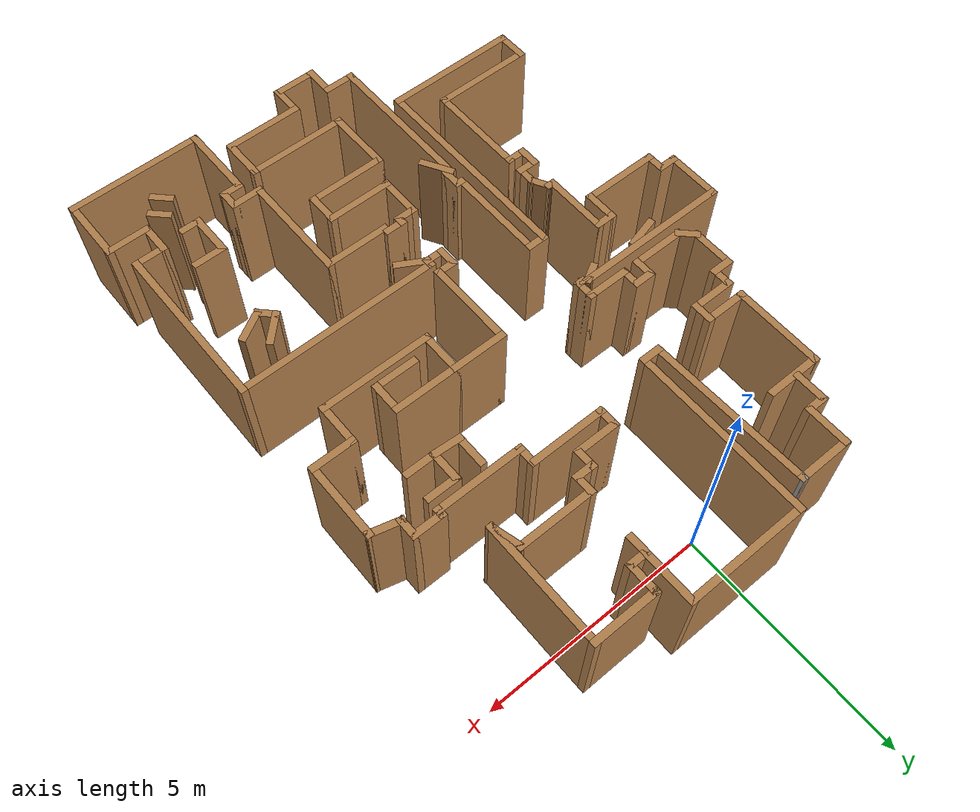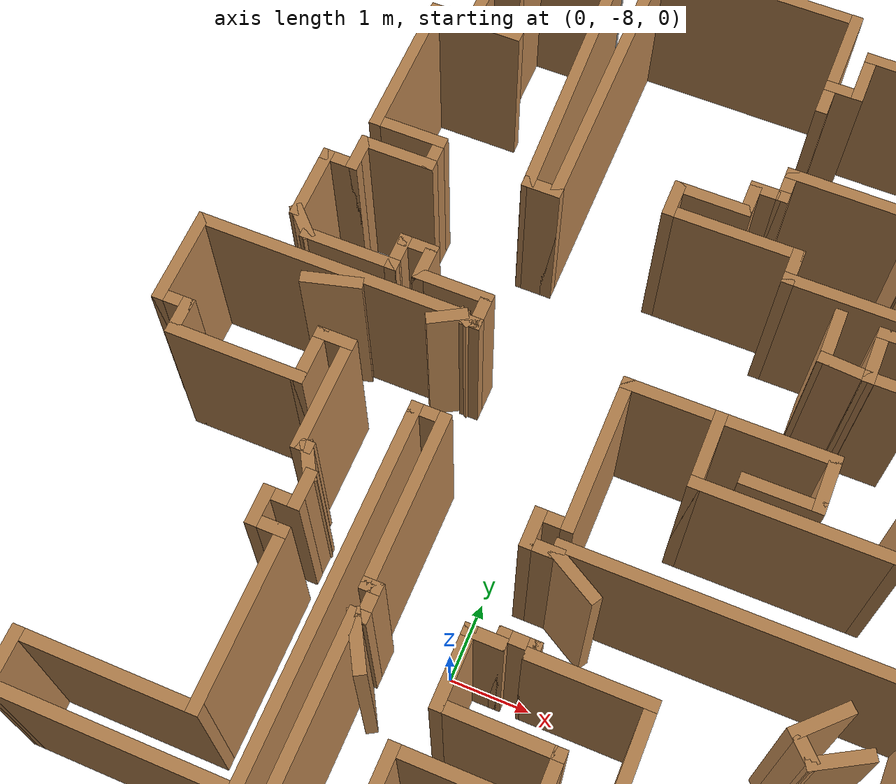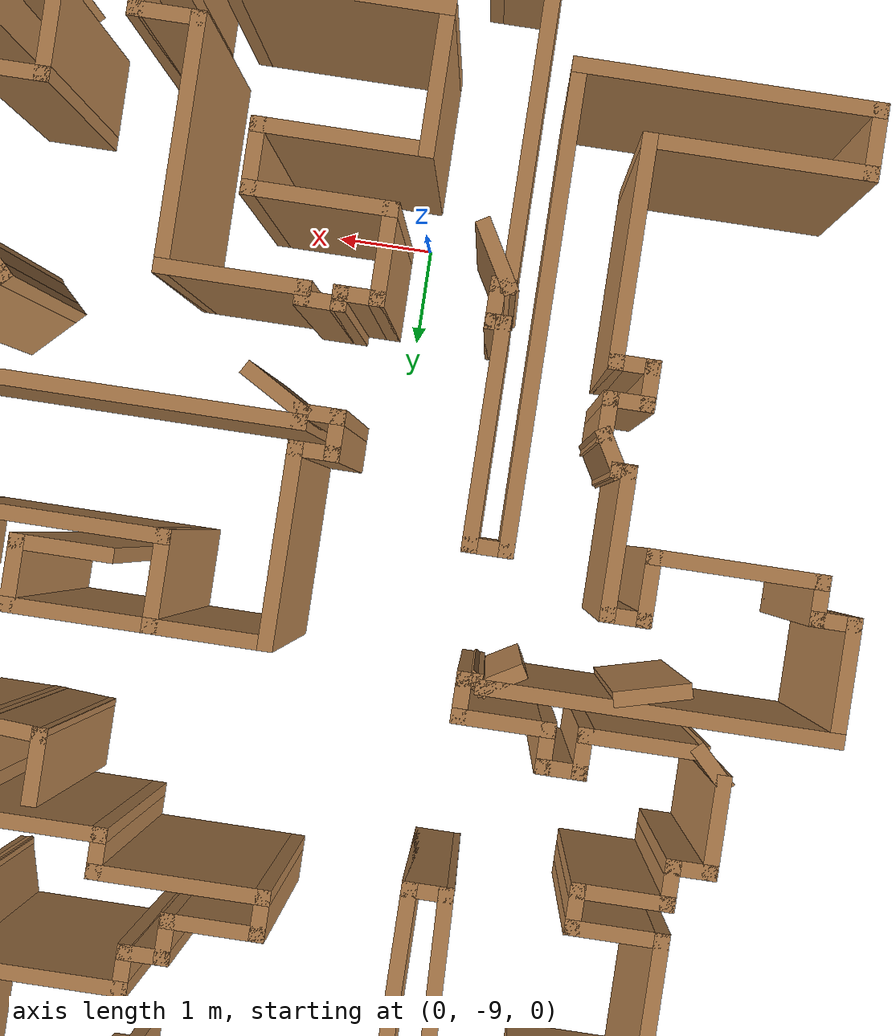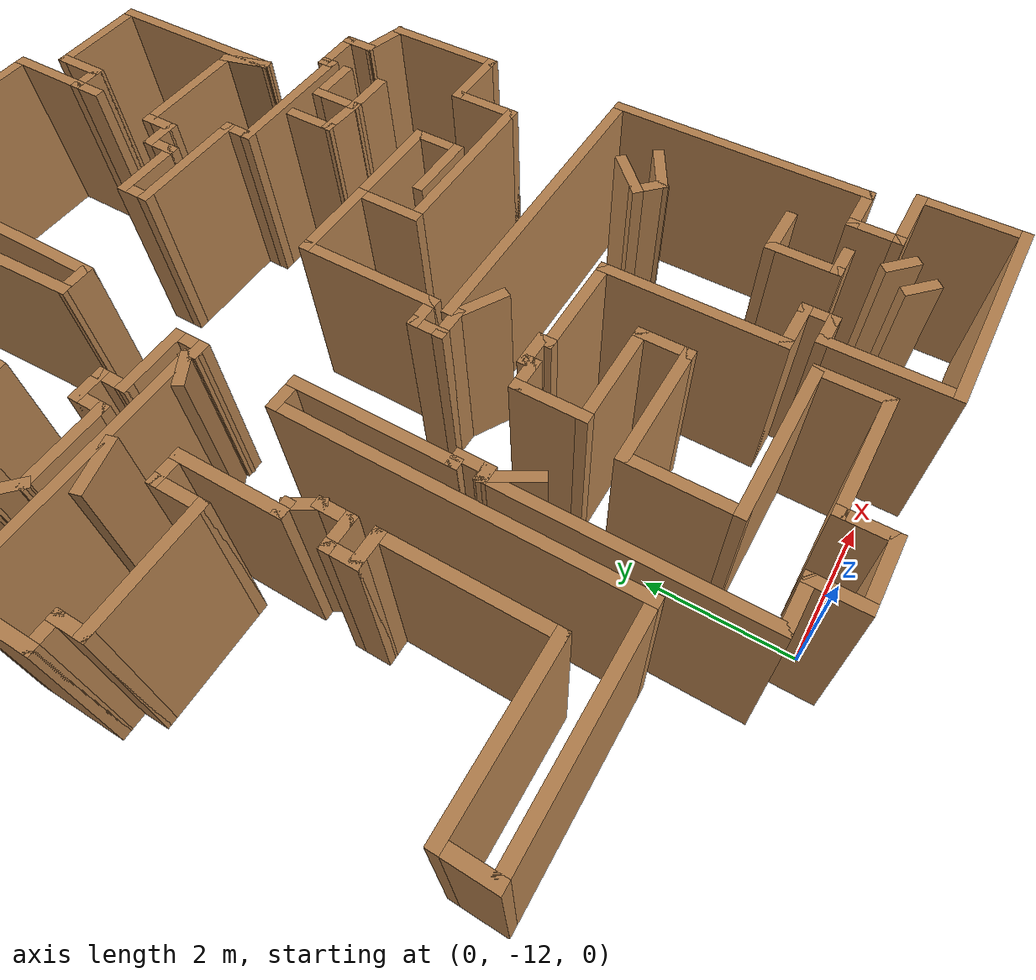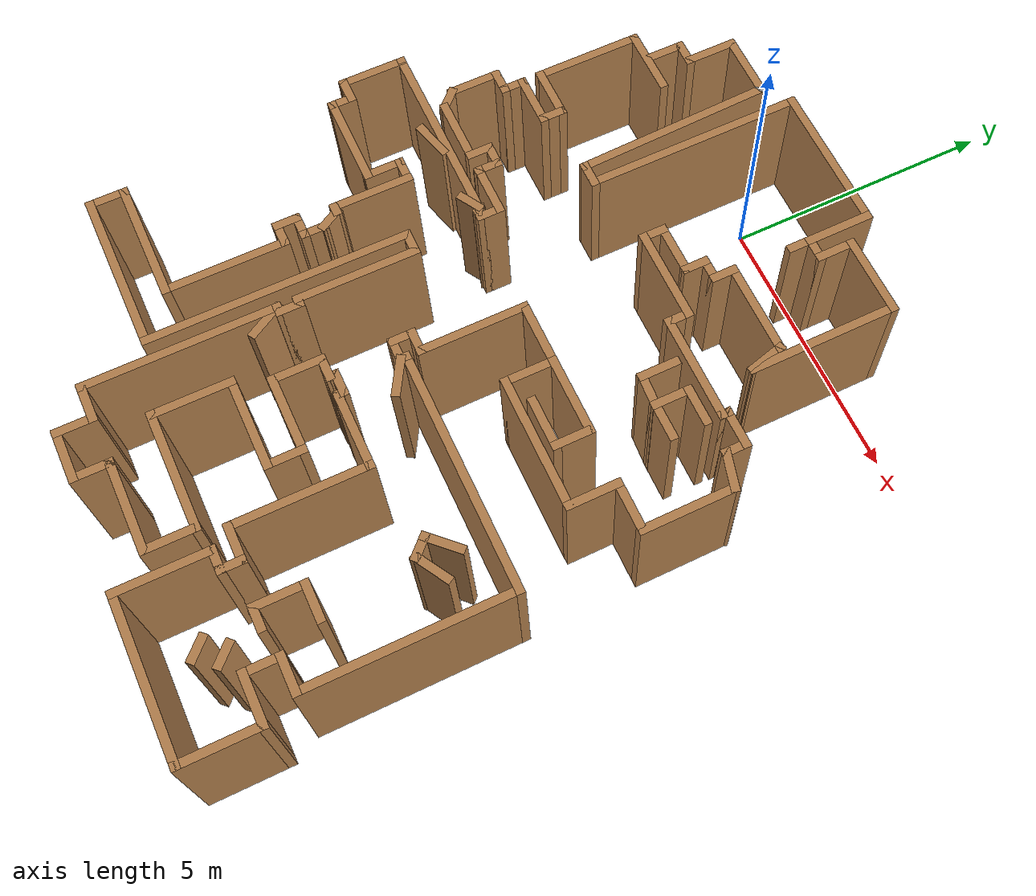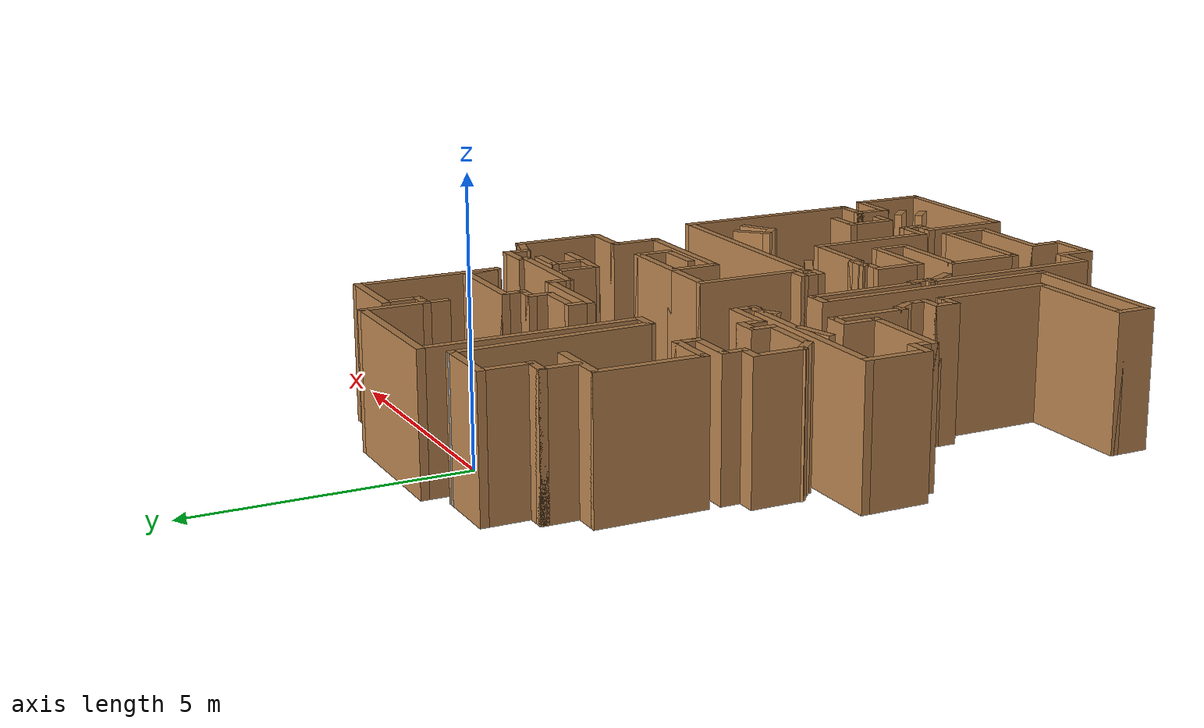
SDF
<?xml version='1.0'?>
<sdf version='1.6'>
  <model name='map_47'>
    <pose frame=''>0.394083 -5.56483 0 0 -0 0</pose>
    <link name='Wall_0'>
      <collision name='Wall_0_Collision'>
        <geometry>
          <box>
            <size>1.25 0.15 2.5</size>
          </box>
        </geometry>
        <pose frame=''>0 0 1.25 0 -0 0</pose>
      </collision>
      <visual name='Wall_0_Visual'>
        <pose frame=''>0 0 1.25 0 -0 0</pose>
        <geometry>
          <box>
            <size>1.25 0.15 2.5</size>
          </box>
        </geometry>
        <material>
          <script>
            <uri>file://media/materials/scripts/gazebo.material</uri>
            <name>Gazebo/Wood</name>
          </script>
          <ambient>1 1 1 1</ambient>
        </material>
        <meta>
          <layer>0</layer>
        </meta>
      </visual>
      <pose frame=''>-2.27237 6.42125 0 0 -0 3.14159</pose>
    </link>
    <link name='Wall_1'>
      <collision name='Wall_1_Collision'>
        <geometry>
          <box>
            <size>1 0.15 2.5</size>
          </box>
        </geometry>
        <pose frame=''>0 0 1.25 0 -0 0</pose>
      </collision>
      <visual name='Wall_1_Visual'>
        <pose frame=''>0 0 1.25 0 -0 0</pose>
        <geometry>
          <box>
            <size>1 0.15 2.5</size>
          </box>
        </geometry>
        <material>
          <script>
            <uri>file://media/materials/scripts/gazebo.material</uri>
            <name>Gazebo/Wood</name>
          </script>
          <ambient>1 1 1 1</ambient>
        </material>
        <meta>
          <layer>0</layer>
        </meta>
      </visual>
      <pose frame=''>-2.82237 5.99625 0 0 -0 -1.5708</pose>
    </link>
    <link name='Wall_10'>
      <collision name='Wall_10_Collision'>
        <geometry>
          <box>
            <size>1 0.15 2.5</size>
          </box>
        </geometry>
        <pose frame=''>0 0 1.25 0 -0 0</pose>
      </collision>
      <visual name='Wall_10_Visual'>
        <pose frame=''>0 0 1.25 0 -0 0</pose>
        <geometry>
          <box>
            <size>1 0.15 2.5</size>
          </box>
        </geometry>
        <material>
          <script>
            <uri>file://media/materials/scripts/gazebo.material</uri>
            <name>Gazebo/Wood</name>
          </script>
          <ambient>1 1 1 1</ambient>
        </material>
        <meta>
          <layer>0</layer>
        </meta>
      </visual>
      <pose frame=''>-3.24838 3.06273 0 0 -0 0</pose>
    </link>
    <link name='Wall_102'>
      <collision name='Wall_102_Collision'>
        <geometry>
          <box>
            <size>4.5 0.15 2.5</size>
          </box>
        </geometry>
        <pose frame=''>0 0 1.25 0 -0 0</pose>
      </collision>
      <visual name='Wall_102_Visual'>
        <pose frame=''>0 0 1.25 0 -0 0</pose>
        <geometry>
          <box>
            <size>4.5 0.15 2.5</size>
          </box>
        </geometry>
        <material>
          <script>
            <uri>file://media/materials/scripts/gazebo.material</uri>
            <name>Gazebo/Wood</name>
          </script>
          <ambient>1 1 1 1</ambient>
        </material>
        <meta>
          <layer>0</layer>
        </meta>
      </visual>
      <pose frame=''>2.5875 -1.23787 0 0 -0 3.14159</pose>
    </link>
    <link name='Wall_105'>
      <collision name='Wall_105_Collision'>
        <geometry>
          <box>
            <size>0.25 0.15 2.5</size>
          </box>
        </geometry>
        <pose frame=''>0 0 1.25 0 -0 0</pose>
      </collision>
      <visual name='Wall_105_Visual'>
        <pose frame=''>0 0 1.25 0 -0 0</pose>
        <geometry>
          <box>
            <size>0.25 0.15 2.5</size>
          </box>
        </geometry>
        <material>
          <script>
            <uri>file://media/materials/scripts/gazebo.material</uri>
            <name>Gazebo/Wood</name>
          </script>
          <ambient>1 1 1 1</ambient>
        </material>
        <meta>
          <layer>0</layer>
        </meta>
      </visual>
      <pose frame=''>0.4125 -1.28787 0 0 -0 -1.5708</pose>
    </link>
    <link name='Wall_106'>
      <collision name='Wall_106_Collision'>
        <geometry>
          <box>
            <size>0.5 0.15 2.5</size>
          </box>
        </geometry>
        <pose frame=''>0 0 1.25 0 -0 0</pose>
      </collision>
      <visual name='Wall_106_Visual'>
        <pose frame=''>0 0 1.25 0 -0 0</pose>
        <geometry>
          <box>
            <size>0.5 0.15 2.5</size>
          </box>
        </geometry>
        <material>
          <script>
            <uri>file://media/materials/scripts/gazebo.material</uri>
            <name>Gazebo/Wood</name>
          </script>
          <ambient>1 1 1 1</ambient>
        </material>
        <meta>
          <layer>0</layer>
        </meta>
      </visual>
      <pose frame=''>0.2375 -1.33787 0 0 -0 3.14159</pose>
    </link>
    <link name='Wall_107'>
      <collision name='Wall_107_Collision'>
        <geometry>
          <box>
            <size>0.5 0.15 2.5</size>
          </box>
        </geometry>
        <pose frame=''>0 0 1.25 0 -0 0</pose>
      </collision>
      <visual name='Wall_107_Visual'>
        <pose frame=''>0 0 1.25 0 -0 0</pose>
        <geometry>
          <box>
            <size>0.5 0.15 2.5</size>
          </box>
        </geometry>
        <material>
          <script>
            <uri>file://media/materials/scripts/gazebo.material</uri>
            <name>Gazebo/Wood</name>
          </script>
          <ambient>1 1 1 1</ambient>
        </material>
        <meta>
          <layer>0</layer>
        </meta>
      </visual>
      <pose frame=''>0.0625 -1.16287 0 0 -0 1.5708</pose>
    </link>
    <link name='Wall_108'>
      <collision name='Wall_108_Collision'>
        <geometry>
          <box>
            <size>0.5 0.15 2.5</size>
          </box>
        </geometry>
        <pose frame=''>0 0 1.25 0 -0 0</pose>
      </collision>
      <visual name='Wall_108_Visual'>
        <pose frame=''>0 0 1.25 0 -0 0</pose>
        <geometry>
          <box>
            <size>0.5 0.15 2.5</size>
          </box>
        </geometry>
        <material>
          <script>
            <uri>file://media/materials/scripts/gazebo.material</uri>
            <name>Gazebo/Wood</name>
          </script>
          <ambient>1 1 1 1</ambient>
        </material>
        <meta>
          <layer>0</layer>
        </meta>
      </visual>
      <pose frame=''>0.2375 -0.987868 0 0 -0 0</pose>
    </link>
    <link name='Wall_109'>
      <collision name='Wall_109_Collision'>
        <geometry>
          <box>
            <size>2 0.15 2.5</size>
          </box>
        </geometry>
        <pose frame=''>0 0 1.25 0 -0 0</pose>
      </collision>
      <visual name='Wall_109_Visual'>
        <pose frame=''>0 0 1.25 0 -0 0</pose>
        <geometry>
          <box>
            <size>2 0.15 2.5</size>
          </box>
        </geometry>
        <material>
          <script>
            <uri>file://media/materials/scripts/gazebo.material</uri>
            <name>Gazebo/Wood</name>
          </script>
          <ambient>1 1 1 1</ambient>
        </material>
        <meta>
          <layer>0</layer>
        </meta>
      </visual>
      <pose frame=''>0.4125 -0.062868 0 0 -0 1.5708</pose>
    </link>
    <link name='Wall_11'>
      <collision name='Wall_11_Collision'>
        <geometry>
          <box>
            <size>0.5 0.15 2.5</size>
          </box>
        </geometry>
        <pose frame=''>0 0 1.25 0 -0 0</pose>
      </collision>
      <visual name='Wall_11_Visual'>
        <pose frame=''>0 0 1.25 0 -0 0</pose>
        <geometry>
          <box>
            <size>0.5 0.15 2.5</size>
          </box>
        </geometry>
        <material>
          <script>
            <uri>file://media/materials/scripts/gazebo.material</uri>
            <name>Gazebo/Wood</name>
          </script>
          <ambient>1 1 1 1</ambient>
        </material>
        <meta>
          <layer>0</layer>
        </meta>
      </visual>
      <pose frame=''>-2.82339 2.88773 0 0 -0 -1.5708</pose>
    </link>
    <link name='Wall_110'>
      <collision name='Wall_110_Collision'>
        <geometry>
          <box>
            <size>1.25 0.15 2.5</size>
          </box>
        </geometry>
        <pose frame=''>0 0 1.25 0 -0 0</pose>
      </collision>
      <visual name='Wall_110_Visual'>
        <pose frame=''>0 0 1.25 0 -0 0</pose>
        <geometry>
          <box>
            <size>1.25 0.15 2.5</size>
          </box>
        </geometry>
        <material>
          <script>
            <uri>file://media/materials/scripts/gazebo.material</uri>
            <name>Gazebo/Wood</name>
          </script>
          <ambient>1 1 1 1</ambient>
        </material>
        <meta>
          <layer>0</layer>
        </meta>
      </visual>
      <pose frame=''>0.9625 0.862132 0 0 -0 0</pose>
    </link>
    <link name='Wall_111'>
      <collision name='Wall_111_Collision'>
        <geometry>
          <box>
            <size>1 0.15 2.5</size>
          </box>
        </geometry>
        <pose frame=''>0 0 1.25 0 -0 0</pose>
      </collision>
      <visual name='Wall_111_Visual'>
        <pose frame=''>0 0 1.25 0 -0 0</pose>
        <geometry>
          <box>
            <size>1 0.15 2.5</size>
          </box>
        </geometry>
        <material>
          <script>
            <uri>file://media/materials/scripts/gazebo.material</uri>
            <name>Gazebo/Wood</name>
          </script>
          <ambient>1 1 1 1</ambient>
        </material>
        <meta>
          <layer>0</layer>
        </meta>
      </visual>
      <pose frame=''>1.5125 0.437132 0 0 -0 -1.5708</pose>
    </link>
    <link name='Wall_112'>
      <collision name='Wall_112_Collision'>
        <geometry>
          <box>
            <size>2.5 0.15 2.5</size>
          </box>
        </geometry>
        <pose frame=''>0 0 1.25 0 -0 0</pose>
      </collision>
      <visual name='Wall_112_Visual'>
        <pose frame=''>0 0 1.25 0 -0 0</pose>
        <geometry>
          <box>
            <size>2.5 0.15 2.5</size>
          </box>
        </geometry>
        <material>
          <script>
            <uri>file://media/materials/scripts/gazebo.material</uri>
            <name>Gazebo/Wood</name>
          </script>
          <ambient>1 1 1 1</ambient>
        </material>
        <meta>
          <layer>0</layer>
        </meta>
      </visual>
      <pose frame=''>2.6875 0.012132 0 0 -0 0</pose>
    </link>
    <link name='Wall_113'>
      <collision name='Wall_113_Collision'>
        <geometry>
          <box>
            <size>1 0.15 2.5</size>
          </box>
        </geometry>
        <pose frame=''>0 0 1.25 0 -0 0</pose>
      </collision>
      <visual name='Wall_113_Visual'>
        <pose frame=''>0 0 1.25 0 -0 0</pose>
        <geometry>
          <box>
            <size>1 0.15 2.5</size>
          </box>
        </geometry>
        <material>
          <script>
            <uri>file://media/materials/scripts/gazebo.material</uri>
            <name>Gazebo/Wood</name>
          </script>
          <ambient>1 1 1 1</ambient>
        </material>
        <meta>
          <layer>0</layer>
        </meta>
      </visual>
      <pose frame=''>3.8625 0.437132 0 0 -0 1.5708</pose>
    </link>
    <link name='Wall_114'>
      <collision name='Wall_114_Collision'>
        <geometry>
          <box>
            <size>1 0.15 2.5</size>
          </box>
        </geometry>
        <pose frame=''>0 0 1.25 0 -0 0</pose>
      </collision>
      <visual name='Wall_114_Visual'>
        <pose frame=''>0 0 1.25 0 -0 0</pose>
        <geometry>
          <box>
            <size>1 0.15 2.5</size>
          </box>
        </geometry>
        <material>
          <script>
            <uri>file://media/materials/scripts/gazebo.material</uri>
            <name>Gazebo/Wood</name>
          </script>
          <ambient>1 1 1 1</ambient>
        </material>
        <meta>
          <layer>0</layer>
        </meta>
      </visual>
      <pose frame=''>4.2875 0.862132 0 0 -0 0</pose>
    </link>
    <link name='Wall_115'>
      <collision name='Wall_115_Collision'>
        <geometry>
          <box>
            <size>1.75 0.15 2.5</size>
          </box>
        </geometry>
        <pose frame=''>0 0 1.25 0 -0 0</pose>
      </collision>
      <visual name='Wall_115_Visual'>
        <pose frame=''>0 0 1.25 0 -0 0</pose>
        <geometry>
          <box>
            <size>1.75 0.15 2.5</size>
          </box>
        </geometry>
        <material>
          <script>
            <uri>file://media/materials/scripts/gazebo.material</uri>
            <name>Gazebo/Wood</name>
          </script>
          <ambient>1 1 1 1</ambient>
        </material>
        <meta>
          <layer>0</layer>
        </meta>
      </visual>
      <pose frame=''>4.7125 1.66213 0 0 -0 1.5708</pose>
    </link>
    <link name='Wall_116'>
      <collision name='Wall_116_Collision'>
        <geometry>
          <box>
            <size>0.75 0.15 2.5</size>
          </box>
        </geometry>
        <pose frame=''>0 0 1.25 0 -0 0</pose>
      </collision>
      <visual name='Wall_116_Visual'>
        <pose frame=''>0 0 1.25 0 -0 0</pose>
        <geometry>
          <box>
            <size>0.75 0.15 2.5</size>
          </box>
        </geometry>
        <material>
          <script>
            <uri>file://media/materials/scripts/gazebo.material</uri>
            <name>Gazebo/Wood</name>
          </script>
          <ambient>1 1 1 1</ambient>
        </material>
        <meta>
          <layer>0</layer>
        </meta>
      </visual>
      <pose frame=''>4.42272 2.53978 0 0 -0 2.87979</pose>
    </link>
    <link name='Wall_117'>
      <collision name='Wall_117_Collision'>
        <geometry>
          <box>
            <size>0.5 0.15 2.5</size>
          </box>
        </geometry>
        <pose frame=''>0 0 1.25 0 -0 0</pose>
      </collision>
      <visual name='Wall_117_Visual'>
        <pose frame=''>0 0 1.25 0 -0 0</pose>
        <geometry>
          <box>
            <size>0.5 0.15 2.5</size>
          </box>
        </geometry>
        <material>
          <script>
            <uri>file://media/materials/scripts/gazebo.material</uri>
            <name>Gazebo/Wood</name>
          </script>
          <ambient>1 1 1 1</ambient>
        </material>
        <meta>
          <layer>0</layer>
        </meta>
      </visual>
      <pose frame=''>4.13295 2.79242 0 0 -0 1.5708</pose>
    </link>
    <link name='Wall_118'>
      <collision name='Wall_118_Collision'>
        <geometry>
          <box>
            <size>0.75 0.15 2.5</size>
          </box>
        </geometry>
        <pose frame=''>0 0 1.25 0 -0 0</pose>
      </collision>
      <visual name='Wall_118_Visual'>
        <pose frame=''>0 0 1.25 0 -0 0</pose>
        <geometry>
          <box>
            <size>0.75 0.15 2.5</size>
          </box>
        </geometry>
        <material>
          <script>
            <uri>file://media/materials/scripts/gazebo.material</uri>
            <name>Gazebo/Wood</name>
          </script>
          <ambient>1 1 1 1</ambient>
        </material>
        <meta>
          <layer>0</layer>
        </meta>
      </visual>
      <pose frame=''>3.83294 2.96742 0 0 -0 3.14159</pose>
    </link>
    <link name='Wall_119'>
      <collision name='Wall_119_Collision'>
        <geometry>
          <box>
            <size>0.25 0.15 2.5</size>
          </box>
        </geometry>
        <pose frame=''>0 0 1.25 0 -0 0</pose>
      </collision>
      <visual name='Wall_119_Visual'>
        <pose frame=''>0 0 1.25 0 -0 0</pose>
        <geometry>
          <box>
            <size>0.25 0.15 2.5</size>
          </box>
        </geometry>
        <material>
          <script>
            <uri>file://media/materials/scripts/gazebo.material</uri>
            <name>Gazebo/Wood</name>
          </script>
          <ambient>1 1 1 1</ambient>
        </material>
        <meta>
          <layer>0</layer>
        </meta>
      </visual>
      <pose frame=''>3.53294 2.91742 0 0 -0 -1.5708</pose>
    </link>
    <link name='Wall_12'>
      <collision name='Wall_12_Collision'>
        <geometry>
          <box>
            <size>1 0.15 2.5</size>
          </box>
        </geometry>
        <pose frame=''>0 0 1.25 0 -0 0</pose>
      </collision>
      <visual name='Wall_12_Visual'>
        <pose frame=''>0 0 1.25 0 -0 0</pose>
        <geometry>
          <box>
            <size>1 0.15 2.5</size>
          </box>
        </geometry>
        <material>
          <script>
            <uri>file://media/materials/scripts/gazebo.material</uri>
            <name>Gazebo/Wood</name>
          </script>
          <ambient>1 1 1 1</ambient>
        </material>
        <meta>
          <layer>0</layer>
        </meta>
      </visual>
      <pose frame=''>-3.24838 2.71273 0 0 -0 3.14159</pose>
    </link>
    <link name='Wall_120'>
      <collision name='Wall_120_Collision'>
        <geometry>
          <box>
            <size>2 0.15 2.5</size>
          </box>
        </geometry>
        <pose frame=''>0 0 1.25 0 -0 0</pose>
      </collision>
      <visual name='Wall_120_Visual'>
        <pose frame=''>0 0 1.25 0 -0 0</pose>
        <geometry>
          <box>
            <size>2 0.15 2.5</size>
          </box>
        </geometry>
        <material>
          <script>
            <uri>file://media/materials/scripts/gazebo.material</uri>
            <name>Gazebo/Wood</name>
          </script>
          <ambient>1 1 1 1</ambient>
        </material>
        <meta>
          <layer>0</layer>
        </meta>
      </visual>
      <pose frame=''>2.60794 2.86742 0 0 -0 3.14159</pose>
    </link>
    <link name='Wall_121'>
      <collision name='Wall_121_Collision'>
        <geometry>
          <box>
            <size>0.5 0.15 2.5</size>
          </box>
        </geometry>
        <pose frame=''>0 0 1.25 0 -0 0</pose>
      </collision>
      <visual name='Wall_121_Visual'>
        <pose frame=''>0 0 1.25 0 -0 0</pose>
        <geometry>
          <box>
            <size>0.5 0.15 2.5</size>
          </box>
        </geometry>
        <material>
          <script>
            <uri>file://media/materials/scripts/gazebo.material</uri>
            <name>Gazebo/Wood</name>
          </script>
          <ambient>1 1 1 1</ambient>
        </material>
        <meta>
          <layer>0</layer>
        </meta>
      </visual>
      <pose frame=''>1.68294 3.04242 0 0 -0 1.5708</pose>
    </link>
    <link name='Wall_122'>
      <collision name='Wall_122_Collision'>
        <geometry>
          <box>
            <size>1.75 0.15 2.5</size>
          </box>
        </geometry>
        <pose frame=''>0 0 1.25 0 -0 0</pose>
      </collision>
      <visual name='Wall_122_Visual'>
        <pose frame=''>0 0 1.25 0 -0 0</pose>
        <geometry>
          <box>
            <size>1.75 0.15 2.5</size>
          </box>
        </geometry>
        <material>
          <script>
            <uri>file://media/materials/scripts/gazebo.material</uri>
            <name>Gazebo/Wood</name>
          </script>
          <ambient>1 1 1 1</ambient>
        </material>
        <meta>
          <layer>0</layer>
        </meta>
      </visual>
      <pose frame=''>0.882944 3.21742 0 0 -0 3.14159</pose>
    </link>
    <link name='Wall_123'>
      <collision name='Wall_123_Collision'>
        <geometry>
          <box>
            <size>0.5 0.15 2.5</size>
          </box>
        </geometry>
        <pose frame=''>0 0 1.25 0 -0 0</pose>
      </collision>
      <visual name='Wall_123_Visual'>
        <pose frame=''>0 0 1.25 0 -0 0</pose>
        <geometry>
          <box>
            <size>0.5 0.15 2.5</size>
          </box>
        </geometry>
        <material>
          <script>
            <uri>file://media/materials/scripts/gazebo.material</uri>
            <name>Gazebo/Wood</name>
          </script>
          <ambient>1 1 1 1</ambient>
        </material>
        <meta>
          <layer>0</layer>
        </meta>
      </visual>
      <pose frame=''>0.082945 3.39242 0 0 -0 1.5708</pose>
    </link>
    <link name='Wall_126'>
      <collision name='Wall_126_Collision'>
        <geometry>
          <box>
            <size>1 0.15 2.5</size>
          </box>
        </geometry>
        <pose frame=''>0 0 1.25 0 -0 0</pose>
      </collision>
      <visual name='Wall_126_Visual'>
        <pose frame=''>0 0 1.25 0 -0 0</pose>
        <geometry>
          <box>
            <size>1 0.15 2.5</size>
          </box>
        </geometry>
        <material>
          <script>
            <uri>file://media/materials/scripts/gazebo.material</uri>
            <name>Gazebo/Wood</name>
          </script>
          <ambient>1 1 1 1</ambient>
        </material>
        <meta>
          <layer>0</layer>
        </meta>
      </visual>
      <pose frame=''>0.507945 3.56742 0 0 -0 0</pose>
    </link>
    <link name='Wall_127'>
      <collision name='Wall_127_Collision'>
        <geometry>
          <box>
            <size>0.5 0.15 2.5</size>
          </box>
        </geometry>
        <pose frame=''>0 0 1.25 0 -0 0</pose>
      </collision>
      <visual name='Wall_127_Visual'>
        <pose frame=''>0 0 1.25 0 -0 0</pose>
        <geometry>
          <box>
            <size>0.5 0.15 2.5</size>
          </box>
        </geometry>
        <material>
          <script>
            <uri>file://media/materials/scripts/gazebo.material</uri>
            <name>Gazebo/Wood</name>
          </script>
          <ambient>1 1 1 1</ambient>
        </material>
        <meta>
          <layer>0</layer>
        </meta>
      </visual>
      <pose frame=''>0.932945 3.74242 0 0 -0 1.5708</pose>
    </link>
    <link name='Wall_128'>
      <collision name='Wall_128_Collision'>
        <geometry>
          <box>
            <size>0.5 0.15 2.5</size>
          </box>
        </geometry>
        <pose frame=''>0 0 1.25 0 -0 0</pose>
      </collision>
      <visual name='Wall_128_Visual'>
        <pose frame=''>0 0 1.25 0 -0 0</pose>
        <geometry>
          <box>
            <size>0.5 0.15 2.5</size>
          </box>
        </geometry>
        <material>
          <script>
            <uri>file://media/materials/scripts/gazebo.material</uri>
            <name>Gazebo/Wood</name>
          </script>
          <ambient>1 1 1 1</ambient>
        </material>
        <meta>
          <layer>0</layer>
        </meta>
      </visual>
      <pose frame=''>1.10794 3.91742 0 0 -0 0</pose>
    </link>
    <link name='Wall_129'>
      <collision name='Wall_129_Collision'>
        <geometry>
          <box>
            <size>0.5 0.15 2.5</size>
          </box>
        </geometry>
        <pose frame=''>0 0 1.25 0 -0 0</pose>
      </collision>
      <visual name='Wall_129_Visual'>
        <pose frame=''>0 0 1.25 0 -0 0</pose>
        <geometry>
          <box>
            <size>0.5 0.15 2.5</size>
          </box>
        </geometry>
        <material>
          <script>
            <uri>file://media/materials/scripts/gazebo.material</uri>
            <name>Gazebo/Wood</name>
          </script>
          <ambient>1 1 1 1</ambient>
        </material>
        <meta>
          <layer>0</layer>
        </meta>
      </visual>
      <pose frame=''>1.28295 4.09242 0 0 -0 1.5708</pose>
    </link>
    <link name='Wall_13'>
      <collision name='Wall_13_Collision'>
        <geometry>
          <box>
            <size>0.5 0.15 2.5</size>
          </box>
        </geometry>
        <pose frame=''>0 0 1.25 0 -0 0</pose>
      </collision>
      <visual name='Wall_13_Visual'>
        <pose frame=''>0 0 1.25 0 -0 0</pose>
        <geometry>
          <box>
            <size>0.5 0.15 2.5</size>
          </box>
        </geometry>
        <material>
          <script>
            <uri>file://media/materials/scripts/gazebo.material</uri>
            <name>Gazebo/Wood</name>
          </script>
          <ambient>1 1 1 1</ambient>
        </material>
        <meta>
          <layer>0</layer>
        </meta>
      </visual>
      <pose frame=''>-3.67339 2.53773 0 0 -0 -1.5708</pose>
    </link>
    <link name='Wall_130'>
      <collision name='Wall_130_Collision'>
        <geometry>
          <box>
            <size>1.75 0.15 2.5</size>
          </box>
        </geometry>
        <pose frame=''>0 0 1.25 0 -0 0</pose>
      </collision>
      <visual name='Wall_130_Visual'>
        <pose frame=''>0 0 1.25 0 -0 0</pose>
        <geometry>
          <box>
            <size>1.75 0.15 2.5</size>
          </box>
        </geometry>
        <material>
          <script>
            <uri>file://media/materials/scripts/gazebo.material</uri>
            <name>Gazebo/Wood</name>
          </script>
          <ambient>1 1 1 1</ambient>
        </material>
        <meta>
          <layer>0</layer>
        </meta>
      </visual>
      <pose frame=''>2.08294 4.26742 0 0 -0 0</pose>
    </link>
    <link name='Wall_131'>
      <collision name='Wall_131_Collision'>
        <geometry>
          <box>
            <size>0.75 0.15 2.5</size>
          </box>
        </geometry>
        <pose frame=''>0 0 1.25 0 -0 0</pose>
      </collision>
      <visual name='Wall_131_Visual'>
        <pose frame=''>0 0 1.25 0 -0 0</pose>
        <geometry>
          <box>
            <size>0.75 0.15 2.5</size>
          </box>
        </geometry>
        <material>
          <script>
            <uri>file://media/materials/scripts/gazebo.material</uri>
            <name>Gazebo/Wood</name>
          </script>
          <ambient>1 1 1 1</ambient>
        </material>
        <meta>
          <layer>0</layer>
        </meta>
      </visual>
      <pose frame=''>2.96059 3.97765 0 0 -0 -1.309</pose>
    </link>
    <link name='Wall_132'>
      <collision name='Wall_132_Collision'>
        <geometry>
          <box>
            <size>2.75 0.15 2.5</size>
          </box>
        </geometry>
        <pose frame=''>0 0 1.25 0 -0 0</pose>
      </collision>
      <visual name='Wall_132_Visual'>
        <pose frame=''>0 0 1.25 0 -0 0</pose>
        <geometry>
          <box>
            <size>2.75 0.15 2.5</size>
          </box>
        </geometry>
        <material>
          <script>
            <uri>file://media/materials/scripts/gazebo.material</uri>
            <name>Gazebo/Wood</name>
          </script>
          <ambient>1 1 1 1</ambient>
        </material>
        <meta>
          <layer>0</layer>
        </meta>
      </visual>
      <pose frame=''>3.03824 4.98787 0 0 -0 1.5708</pose>
    </link>
    <link name='Wall_133'>
      <collision name='Wall_133_Collision'>
        <geometry>
          <box>
            <size>1.5 0.15 2.5</size>
          </box>
        </geometry>
        <pose frame=''>0 0 1.25 0 -0 0</pose>
      </collision>
      <visual name='Wall_133_Visual'>
        <pose frame=''>0 0 1.25 0 -0 0</pose>
        <geometry>
          <box>
            <size>1.5 0.15 2.5</size>
          </box>
        </geometry>
        <material>
          <script>
            <uri>file://media/materials/scripts/gazebo.material</uri>
            <name>Gazebo/Wood</name>
          </script>
          <ambient>1 1 1 1</ambient>
        </material>
        <meta>
          <layer>0</layer>
        </meta>
      </visual>
      <pose frame=''>2.36324 6.28787 0 0 -0 3.14159</pose>
    </link>
    <link name='Wall_134'>
      <collision name='Wall_134_Collision'>
        <geometry>
          <box>
            <size>0.75 0.15 2.5</size>
          </box>
        </geometry>
        <pose frame=''>0 0 1.25 0 -0 0</pose>
      </collision>
      <visual name='Wall_134_Visual'>
        <pose frame=''>0 0 1.25 0 -0 0</pose>
        <geometry>
          <box>
            <size>0.75 0.15 2.5</size>
          </box>
        </geometry>
        <material>
          <script>
            <uri>file://media/materials/scripts/gazebo.material</uri>
            <name>Gazebo/Wood</name>
          </script>
          <ambient>1 1 1 1</ambient>
        </material>
        <meta>
          <layer>0</layer>
        </meta>
      </visual>
      <pose frame=''>1.68824 5.98787 0 0 -0 -1.5708</pose>
    </link>
    <link name='Wall_135'>
      <collision name='Wall_135_Collision'>
        <geometry>
          <box>
            <size>0.5 0.15 2.5</size>
          </box>
        </geometry>
        <pose frame=''>0 0 1.25 0 -0 0</pose>
      </collision>
      <visual name='Wall_135_Visual'>
        <pose frame=''>0 0 1.25 0 -0 0</pose>
        <geometry>
          <box>
            <size>0.5 0.15 2.5</size>
          </box>
        </geometry>
        <material>
          <script>
            <uri>file://media/materials/scripts/gazebo.material</uri>
            <name>Gazebo/Wood</name>
          </script>
          <ambient>1 1 1 1</ambient>
        </material>
        <meta>
          <layer>0</layer>
        </meta>
      </visual>
      <pose frame=''>1.51324 5.68787 0 0 -0 3.14159</pose>
    </link>
    <link name='Wall_136'>
      <collision name='Wall_136_Collision'>
        <geometry>
          <box>
            <size>1.25 0.15 2.5</size>
          </box>
        </geometry>
        <pose frame=''>0 0 1.25 0 -0 0</pose>
      </collision>
      <visual name='Wall_136_Visual'>
        <pose frame=''>0 0 1.25 0 -0 0</pose>
        <geometry>
          <box>
            <size>1.25 0.15 2.5</size>
          </box>
        </geometry>
        <material>
          <script>
            <uri>file://media/materials/scripts/gazebo.material</uri>
            <name>Gazebo/Wood</name>
          </script>
          <ambient>1 1 1 1</ambient>
        </material>
        <meta>
          <layer>0</layer>
        </meta>
      </visual>
      <pose frame=''>1.33824 6.23787 0 0 -0 1.5708</pose>
    </link>
    <link name='Wall_137'>
      <collision name='Wall_137_Collision'>
        <geometry>
          <box>
            <size>2.75 0.15 2.5</size>
          </box>
        </geometry>
        <pose frame=''>0 0 1.25 0 -0 0</pose>
      </collision>
      <visual name='Wall_137_Visual'>
        <pose frame=''>0 0 1.25 0 -0 0</pose>
        <geometry>
          <box>
            <size>2.75 0.15 2.5</size>
          </box>
        </geometry>
        <material>
          <script>
            <uri>file://media/materials/scripts/gazebo.material</uri>
            <name>Gazebo/Wood</name>
          </script>
          <ambient>1 1 1 1</ambient>
        </material>
        <meta>
          <layer>0</layer>
        </meta>
      </visual>
      <pose frame=''>0.038236 6.78787 0 0 -0 3.14159</pose>
    </link>
    <link name='Wall_138'>
      <collision name='Wall_138_Collision'>
        <geometry>
          <box>
            <size>4 0.15 2.5</size>
          </box>
        </geometry>
        <pose frame=''>0 0 1.25 0 -0 0</pose>
      </collision>
      <visual name='Wall_138_Visual'>
        <pose frame=''>0 0 1.25 0 -0 0</pose>
        <geometry>
          <box>
            <size>4 0.15 2.5</size>
          </box>
        </geometry>
        <material>
          <script>
            <uri>file://media/materials/scripts/gazebo.material</uri>
            <name>Gazebo/Wood</name>
          </script>
          <ambient>1 1 1 1</ambient>
        </material>
        <meta>
          <layer>0</layer>
        </meta>
      </visual>
      <pose frame=''>-1.26176 4.86287 0 0 -0 -1.5708</pose>
    </link>
    <link name='Wall_139'>
      <collision name='Wall_139_Collision'>
        <geometry>
          <box>
            <size>0.5 0.15 2.5</size>
          </box>
        </geometry>
        <pose frame=''>0 0 1.25 0 -0 0</pose>
      </collision>
      <visual name='Wall_139_Visual'>
        <pose frame=''>0 0 1.25 0 -0 0</pose>
        <geometry>
          <box>
            <size>0.5 0.15 2.5</size>
          </box>
        </geometry>
        <material>
          <script>
            <uri>file://media/materials/scripts/gazebo.material</uri>
            <name>Gazebo/Wood</name>
          </script>
          <ambient>1 1 1 1</ambient>
        </material>
        <meta>
          <layer>0</layer>
        </meta>
      </visual>
      <pose frame=''>-1.43676 2.93787 0 0 -0 3.14159</pose>
    </link>
    <link name='Wall_141'>
      <collision name='Wall_141_Collision'>
        <geometry>
          <box>
            <size>0.15 0.15 2.5</size>
          </box>
        </geometry>
        <pose frame=''>0 0 1.25 0 -0 0</pose>
      </collision>
      <visual name='Wall_141_Visual'>
        <pose frame=''>0 0 1.25 0 -0 0</pose>
        <geometry>
          <box>
            <size>0.15 0.15 2.5</size>
          </box>
        </geometry>
        <material>
          <script>
            <uri>file://media/materials/scripts/gazebo.material</uri>
            <name>Gazebo/Grey</name>
          </script>
          <ambient>1 1 1 1</ambient>
        </material>
        <meta>
          <layer>0</layer>
        </meta>
      </visual>
      <pose frame=''>-1.72237 6.42125 0 0 -0 0</pose>
    </link>
    <link name='Wall_144'>
      <collision name='Wall_144_Collision'>
        <geometry>
          <box>
            <size>3.63513 0.15 2.5</size>
          </box>
        </geometry>
        <pose frame=''>0 0 1.25 0 -0 0</pose>
      </collision>
      <visual name='Wall_144_Visual'>
        <pose frame=''>0 0 1.25 0 -0 0</pose>
        <geometry>
          <box>
            <size>3.63513 0.15 2.5</size>
          </box>
        </geometry>
        <material>
          <script>
            <uri>file://media/materials/scripts/gazebo.material</uri>
            <name>Gazebo/Wood</name>
          </script>
          <ambient>1 1 1 1</ambient>
        </material>
        <meta>
          <layer>0</layer>
        </meta>
      </visual>
      <pose frame=''>-1.66707 4.67956 0 0 -0 1.60254</pose>
    </link>
    <link name='Wall_146'>
      <collision name='Wall_146_Collision'>
        <geometry>
          <box>
            <size>0.5 0.15 2.5</size>
          </box>
        </geometry>
        <pose frame=''>0 0 1.25 0 -0 0</pose>
      </collision>
      <visual name='Wall_146_Visual'>
        <pose frame=''>0 0 1.25 0 -0 0</pose>
        <geometry>
          <box>
            <size>0.5 0.15 2.5</size>
          </box>
        </geometry>
        <material>
          <script>
            <uri>file://media/materials/scripts/gazebo.material</uri>
            <name>Gazebo/Wood</name>
          </script>
          <ambient>1 1 1 1</ambient>
        </material>
        <meta>
          <layer>0</layer>
        </meta>
      </visual>
      <pose frame=''>1.33824 5.51287 0 0 -0 -1.5708</pose>
    </link>
    <link name='Wall_148'>
      <collision name='Wall_148_Collision'>
        <geometry>
          <box>
            <size>0.75 0.15 2.5</size>
          </box>
        </geometry>
        <pose frame=''>0 0 1.25 0 -0 0</pose>
      </collision>
      <visual name='Wall_148_Visual'>
        <pose frame=''>0 0 1.25 0 -0 0</pose>
        <geometry>
          <box>
            <size>0.75 0.15 2.5</size>
          </box>
        </geometry>
        <material>
          <script>
            <uri>file://media/materials/scripts/gazebo.material</uri>
            <name>Gazebo/Wood</name>
          </script>
          <ambient>1 1 1 1</ambient>
        </material>
        <meta>
          <layer>0</layer>
        </meta>
      </visual>
      <pose frame=''>3.21399 2.5924 0 0 -0 3.14159</pose>
    </link>
    <link name='Wall_149'>
      <collision name='Wall_149_Collision'>
        <geometry>
          <box>
            <size>0.75 0.15 2.5</size>
          </box>
        </geometry>
        <pose frame=''>0 0 1.25 0 -0 0</pose>
      </collision>
      <visual name='Wall_149_Visual'>
        <pose frame=''>0 0 1.25 0 -0 0</pose>
        <geometry>
          <box>
            <size>0.75 0.15 2.5</size>
          </box>
        </geometry>
        <material>
          <script>
            <uri>file://media/materials/scripts/gazebo.material</uri>
            <name>Gazebo/Wood</name>
          </script>
          <ambient>1 1 1 1</ambient>
        </material>
        <meta>
          <layer>0</layer>
        </meta>
      </visual>
      <pose frame=''>2.91399 2.2924 0 0 -0 -1.5708</pose>
    </link>
    <link name='Wall_150'>
      <collision name='Wall_150_Collision'>
        <geometry>
          <box>
            <size>0.75 0.15 2.5</size>
          </box>
        </geometry>
        <pose frame=''>0 0 1.25 0 -0 0</pose>
      </collision>
      <visual name='Wall_150_Visual'>
        <pose frame=''>0 0 1.25 0 -0 0</pose>
        <geometry>
          <box>
            <size>0.75 0.15 2.5</size>
          </box>
        </geometry>
        <material>
          <script>
            <uri>file://media/materials/scripts/gazebo.material</uri>
            <name>Gazebo/Wood</name>
          </script>
          <ambient>1 1 1 1</ambient>
        </material>
        <meta>
          <layer>0</layer>
        </meta>
      </visual>
      <pose frame=''>3.21399 1.9924 0 0 -0 0</pose>
    </link>
    <link name='Wall_152'>
      <collision name='Wall_152_Collision'>
        <geometry>
          <box>
            <size>0.75 0.15 2.5</size>
          </box>
        </geometry>
        <pose frame=''>0 0 1.25 0 -0 0</pose>
      </collision>
      <visual name='Wall_152_Visual'>
        <pose frame=''>0 0 1.25 0 -0 0</pose>
        <geometry>
          <box>
            <size>0.75 0.15 2.5</size>
          </box>
        </geometry>
        <material>
          <script>
            <uri>file://media/materials/scripts/gazebo.material</uri>
            <name>Gazebo/Wood</name>
          </script>
          <ambient>1 1 1 1</ambient>
        </material>
        <meta>
          <layer>0</layer>
        </meta>
      </visual>
      <pose frame=''>2.37714 2.32738 0 0 -0 -1.5708</pose>
    </link>
    <link name='Wall_153'>
      <collision name='Wall_153_Collision'>
        <geometry>
          <box>
            <size>0.687992 0.15 2.5</size>
          </box>
        </geometry>
        <pose frame=''>0 0 1.25 0 -0 0</pose>
      </collision>
      <visual name='Wall_153_Visual'>
        <pose frame=''>0 0 1.25 0 -0 0</pose>
        <geometry>
          <box>
            <size>0.687992 0.15 2.5</size>
          </box>
        </geometry>
        <material>
          <script>
            <uri>file://media/materials/scripts/gazebo.material</uri>
            <name>Gazebo/Wood</name>
          </script>
          <ambient>1 1 1 1</ambient>
        </material>
        <meta>
          <layer>0</layer>
        </meta>
      </visual>
      <pose frame=''>2.64557 2.00989 0 0 -0 -0.065066</pose>
    </link>
    <link name='Wall_156'>
      <collision name='Wall_156_Collision'>
        <geometry>
          <box>
            <size>1.5 0.15 2.5</size>
          </box>
        </geometry>
        <pose frame=''>0 0 1.25 0 -0 0</pose>
      </collision>
      <visual name='Wall_156_Visual'>
        <pose frame=''>0 0 1.25 0 -0 0</pose>
        <geometry>
          <box>
            <size>1.5 0.15 2.5</size>
          </box>
        </geometry>
        <material>
          <script>
            <uri>file://media/materials/scripts/gazebo.material</uri>
            <name>Gazebo/Wood</name>
          </script>
          <ambient>1 1 1 1</ambient>
        </material>
        <meta>
          <layer>0</layer>
        </meta>
      </visual>
      <pose frame=''>2.1875 0.862132 0 0 -0 0</pose>
    </link>
    <link name='Wall_157'>
      <collision name='Wall_157_Collision'>
        <geometry>
          <box>
            <size>0.75 0.15 2.5</size>
          </box>
        </geometry>
        <pose frame=''>0 0 1.25 0 -0 0</pose>
      </collision>
      <visual name='Wall_157_Visual'>
        <pose frame=''>0 0 1.25 0 -0 0</pose>
        <geometry>
          <box>
            <size>0.75 0.15 2.5</size>
          </box>
        </geometry>
        <material>
          <script>
            <uri>file://media/materials/scripts/gazebo.material</uri>
            <name>Gazebo/Wood</name>
          </script>
          <ambient>1 1 1 1</ambient>
        </material>
        <meta>
          <layer>0</layer>
        </meta>
      </visual>
      <pose frame=''>2.8625 0.562132 0 0 -0 -1.5708</pose>
    </link>
    <link name='Wall_158'>
      <collision name='Wall_158_Collision'>
        <geometry>
          <box>
            <size>1 0.15 2.5</size>
          </box>
        </geometry>
        <pose frame=''>0 0 1.25 0 -0 0</pose>
      </collision>
      <visual name='Wall_158_Visual'>
        <pose frame=''>0 0 1.25 0 -0 0</pose>
        <geometry>
          <box>
            <size>1 0.15 2.5</size>
          </box>
        </geometry>
        <material>
          <script>
            <uri>file://media/materials/scripts/gazebo.material</uri>
            <name>Gazebo/Wood</name>
          </script>
          <ambient>1 1 1 1</ambient>
        </material>
        <meta>
          <layer>0</layer>
        </meta>
      </visual>
      <pose frame=''>2.4375 0.262132 0 0 -0 3.14159</pose>
    </link>
    <link name='Wall_16'>
      <collision name='Wall_16_Collision'>
        <geometry>
          <box>
            <size>0.5 0.15 2.5</size>
          </box>
        </geometry>
        <pose frame=''>0 0 1.25 0 -0 0</pose>
      </collision>
      <visual name='Wall_16_Visual'>
        <pose frame=''>0 0 1.25 0 -0 0</pose>
        <geometry>
          <box>
            <size>0.5 0.15 2.5</size>
          </box>
        </geometry>
        <material>
          <script>
            <uri>file://media/materials/scripts/gazebo.material</uri>
            <name>Gazebo/Wood</name>
          </script>
          <ambient>1 1 1 1</ambient>
        </material>
        <meta>
          <layer>0</layer>
        </meta>
      </visual>
      <pose frame=''>-3.84838 2.36273 0 0 -0 3.14159</pose>
    </link>
    <link name='Wall_164'>
      <collision name='Wall_164_Collision'>
        <geometry>
          <box>
            <size>0.5 0.15 2.5</size>
          </box>
        </geometry>
        <pose frame=''>0 0 1.25 0 -0 0</pose>
      </collision>
      <visual name='Wall_164_Visual'>
        <pose frame=''>0 0 1.25 0 -0 0</pose>
        <geometry>
          <box>
            <size>0.5 0.15 2.5</size>
          </box>
        </geometry>
        <material>
          <script>
            <uri>file://media/materials/scripts/gazebo.material</uri>
            <name>Gazebo/Wood</name>
          </script>
          <ambient>1 1 1 1</ambient>
        </material>
        <meta>
          <layer>0</layer>
        </meta>
      </visual>
      <pose frame=''>-1.81405 0.877741 0 0 -0 -2.61799</pose>
    </link>
    <link name='Wall_166'>
      <collision name='Wall_166_Collision'>
        <geometry>
          <box>
            <size>0.75 0.15 2.5</size>
          </box>
        </geometry>
        <pose frame=''>0 0 1.25 0 -0 0</pose>
      </collision>
      <visual name='Wall_166_Visual'>
        <pose frame=''>0 0 1.25 0 -0 0</pose>
        <geometry>
          <box>
            <size>0.75 0.15 2.5</size>
          </box>
        </geometry>
        <material>
          <script>
            <uri>file://media/materials/scripts/gazebo.material</uri>
            <name>Gazebo/Wood</name>
          </script>
          <ambient>1 1 1 1</ambient>
        </material>
        <meta>
          <layer>0</layer>
        </meta>
      </visual>
      <pose frame=''>-3.24472 0.798606 0 0 -0 0.261799</pose>
    </link>
    <link name='Wall_169'>
      <collision name='Wall_169_Collision'>
        <geometry>
          <box>
            <size>0.75 0.15 2.5</size>
          </box>
        </geometry>
        <pose frame=''>0 0 1.25 0 -0 0</pose>
      </collision>
      <visual name='Wall_169_Visual'>
        <pose frame=''>0 0 1.25 0 -0 0</pose>
        <geometry>
          <box>
            <size>0.75 0.15 2.5</size>
          </box>
        </geometry>
        <material>
          <script>
            <uri>file://media/materials/scripts/gazebo.material</uri>
            <name>Gazebo/Wood</name>
          </script>
          <ambient>1 1 1 1</ambient>
        </material>
        <meta>
          <layer>0</layer>
        </meta>
      </visual>
      <pose frame=''>0.672308 -1.48787 0 0 -0 -0.523599</pose>
    </link>
    <link name='Wall_17'>
      <collision name='Wall_17_Collision'>
        <geometry>
          <box>
            <size>1 0.15 2.5</size>
          </box>
        </geometry>
        <pose frame=''>0 0 1.25 0 -0 0</pose>
      </collision>
      <visual name='Wall_17_Visual'>
        <pose frame=''>0 0 1.25 0 -0 0</pose>
        <geometry>
          <box>
            <size>1 0.15 2.5</size>
          </box>
        </geometry>
        <material>
          <script>
            <uri>file://media/materials/scripts/gazebo.material</uri>
            <name>Gazebo/Wood</name>
          </script>
          <ambient>1 1 1 1</ambient>
        </material>
        <meta>
          <layer>0</layer>
        </meta>
      </visual>
      <pose frame=''>-4.02339 1.93773 0 0 -0 -1.5708</pose>
    </link>
    <link name='Wall_171'>
      <collision name='Wall_171_Collision'>
        <geometry>
          <box>
            <size>0.75 0.15 2.5</size>
          </box>
        </geometry>
        <pose frame=''>0 0 1.25 0 -0 0</pose>
      </collision>
      <visual name='Wall_171_Visual'>
        <pose frame=''>0 0 1.25 0 -0 0</pose>
        <geometry>
          <box>
            <size>0.75 0.15 2.5</size>
          </box>
        </geometry>
        <material>
          <script>
            <uri>file://media/materials/scripts/gazebo.material</uri>
            <name>Gazebo/Wood</name>
          </script>
          <ambient>1 1 1 1</ambient>
        </material>
        <meta>
          <layer>0</layer>
        </meta>
      </visual>
      <pose frame=''>3.57602 -1.97786 0 0 -0 -2.35619</pose>
    </link>
    <link name='Wall_172'>
      <collision name='Wall_172_Collision'>
        <geometry>
          <box>
            <size>0.5 0.15 2.5</size>
          </box>
        </geometry>
        <pose frame=''>0 0 1.25 0 -0 0</pose>
      </collision>
      <visual name='Wall_172_Visual'>
        <pose frame=''>0 0 1.25 0 -0 0</pose>
        <geometry>
          <box>
            <size>0.5 0.15 2.5</size>
          </box>
        </geometry>
        <material>
          <script>
            <uri>file://media/materials/scripts/gazebo.material</uri>
            <name>Gazebo/Wood</name>
          </script>
          <ambient>1 1 1 1</ambient>
        </material>
        <meta>
          <layer>0</layer>
        </meta>
      </visual>
      <pose frame=''>3.48763 -2.31373 0 0 -0 -0.785398</pose>
    </link>
    <link name='Wall_173'>
      <collision name='Wall_173_Collision'>
        <geometry>
          <box>
            <size>0.75 0.15 2.5</size>
          </box>
        </geometry>
        <pose frame=''>0 0 1.25 0 -0 0</pose>
      </collision>
      <visual name='Wall_173_Visual'>
        <pose frame=''>0 0 1.25 0 -0 0</pose>
        <geometry>
          <box>
            <size>0.75 0.15 2.5</size>
          </box>
        </geometry>
        <material>
          <script>
            <uri>file://media/materials/scripts/gazebo.material</uri>
            <name>Gazebo/Wood</name>
          </script>
          <ambient>1 1 1 1</ambient>
        </material>
        <meta>
          <layer>0</layer>
        </meta>
      </visual>
      <pose frame=''>3.87118 -2.28748 0 0 -0 0.523599</pose>
    </link>
    <link name='Wall_175'>
      <collision name='Wall_175_Collision'>
        <geometry>
          <box>
            <size>0.75 0.15 2.5</size>
          </box>
        </geometry>
        <pose frame=''>0 0 1.25 0 -0 0</pose>
      </collision>
      <visual name='Wall_175_Visual'>
        <pose frame=''>0 0 1.25 0 -0 0</pose>
        <geometry>
          <box>
            <size>0.75 0.15 2.5</size>
          </box>
        </geometry>
        <material>
          <script>
            <uri>file://media/materials/scripts/gazebo.material</uri>
            <name>Gazebo/Wood</name>
          </script>
          <ambient>1 1 1 1</ambient>
        </material>
        <meta>
          <layer>0</layer>
        </meta>
      </visual>
      <pose frame=''>3.58067 -4.10192 0 0 -0 3.14159</pose>
    </link>
    <link name='Wall_176'>
      <collision name='Wall_176_Collision'>
        <geometry>
          <box>
            <size>1 0.15 2.5</size>
          </box>
        </geometry>
        <pose frame=''>0 0 1.25 0 -0 0</pose>
      </collision>
      <visual name='Wall_176_Visual'>
        <pose frame=''>0 0 1.25 0 -0 0</pose>
        <geometry>
          <box>
            <size>1 0.15 2.5</size>
          </box>
        </geometry>
        <material>
          <script>
            <uri>file://media/materials/scripts/gazebo.material</uri>
            <name>Gazebo/Wood</name>
          </script>
          <ambient>1 1 1 1</ambient>
        </material>
        <meta>
          <layer>0</layer>
        </meta>
      </visual>
      <pose frame=''>3.28067 -4.52692 0 0 -0 -1.5708</pose>
    </link>
    <link name='Wall_179'>
      <collision name='Wall_179_Collision'>
        <geometry>
          <box>
            <size>0.5 0.15 2.5</size>
          </box>
        </geometry>
        <pose frame=''>0 0 1.25 0 -0 0</pose>
      </collision>
      <visual name='Wall_179_Visual'>
        <pose frame=''>0 0 1.25 0 -0 0</pose>
        <geometry>
          <box>
            <size>0.5 0.15 2.5</size>
          </box>
        </geometry>
        <material>
          <script>
            <uri>file://media/materials/scripts/gazebo.material</uri>
            <name>Gazebo/Wood</name>
          </script>
          <ambient>1 1 1 1</ambient>
        </material>
        <meta>
          <layer>0</layer>
        </meta>
      </visual>
      <pose frame=''>3.45567 -4.95192 0 0 -0 0</pose>
    </link>
    <link name='Wall_18'>
      <collision name='Wall_18_Collision'>
        <geometry>
          <box>
            <size>0.5 0.15 2.5</size>
          </box>
        </geometry>
        <pose frame=''>0 0 1.25 0 -0 0</pose>
      </collision>
      <visual name='Wall_18_Visual'>
        <pose frame=''>0 0 1.25 0 -0 0</pose>
        <geometry>
          <box>
            <size>0.5 0.15 2.5</size>
          </box>
        </geometry>
        <material>
          <script>
            <uri>file://media/materials/scripts/gazebo.material</uri>
            <name>Gazebo/Wood</name>
          </script>
          <ambient>1 1 1 1</ambient>
        </material>
        <meta>
          <layer>0</layer>
        </meta>
      </visual>
      <pose frame=''>-3.89964 1.38898 0 0 -0 -0.785398</pose>
    </link>
    <link name='Wall_181'>
      <collision name='Wall_181_Collision'>
        <geometry>
          <box>
            <size>0.5 0.15 2.5</size>
          </box>
        </geometry>
        <pose frame=''>0 0 1.25 0 -0 0</pose>
      </collision>
      <visual name='Wall_181_Visual'>
        <pose frame=''>0 0 1.25 0 -0 0</pose>
        <geometry>
          <box>
            <size>0.5 0.15 2.5</size>
          </box>
        </geometry>
        <material>
          <script>
            <uri>file://media/materials/scripts/gazebo.material</uri>
            <name>Gazebo/Wood</name>
          </script>
          <ambient>1 1 1 1</ambient>
        </material>
        <meta>
          <layer>0</layer>
        </meta>
      </visual>
      <pose frame=''>3.77311 -5.59037 0 0 -0 -0.785398</pose>
    </link>
    <link name='Wall_183'>
      <collision name='Wall_183_Collision'>
        <geometry>
          <box>
            <size>0.5 0.15 2.5</size>
          </box>
        </geometry>
        <pose frame=''>0 0 1.25 0 -0 0</pose>
      </collision>
      <visual name='Wall_183_Visual'>
        <pose frame=''>0 0 1.25 0 -0 0</pose>
        <geometry>
          <box>
            <size>0.5 0.15 2.5</size>
          </box>
        </geometry>
        <material>
          <script>
            <uri>file://media/materials/scripts/gazebo.material</uri>
            <name>Gazebo/Wood</name>
          </script>
          <ambient>1 1 1 1</ambient>
        </material>
        <meta>
          <layer>0</layer>
        </meta>
      </visual>
      <pose frame=''>3.51867 -5.9142 0 0 -0 -0.785398</pose>
    </link>
    <link name='Wall_185'>
      <collision name='Wall_185_Collision'>
        <geometry>
          <box>
            <size>0.75 0.15 2.5</size>
          </box>
        </geometry>
        <pose frame=''>0 0 1.25 0 -0 0</pose>
      </collision>
      <visual name='Wall_185_Visual'>
        <pose frame=''>0 0 1.25 0 -0 0</pose>
        <geometry>
          <box>
            <size>0.75 0.15 2.5</size>
          </box>
        </geometry>
        <material>
          <script>
            <uri>file://media/materials/scripts/gazebo.material</uri>
            <name>Gazebo/Wood</name>
          </script>
          <ambient>1 1 1 1</ambient>
        </material>
        <meta>
          <layer>0</layer>
        </meta>
      </visual>
      <pose frame=''>-1.1875 -3.04768 0 0 -0 -1.0472</pose>
    </link>
    <link name='Wall_19'>
      <collision name='Wall_19_Collision'>
        <geometry>
          <box>
            <size>1.25 0.15 2.5</size>
          </box>
        </geometry>
        <pose frame=''>0 0 1.25 0 -0 0</pose>
      </collision>
      <visual name='Wall_19_Visual'>
        <pose frame=''>0 0 1.25 0 -0 0</pose>
        <geometry>
          <box>
            <size>1.25 0.15 2.5</size>
          </box>
        </geometry>
        <material>
          <script>
            <uri>file://media/materials/scripts/gazebo.material</uri>
            <name>Gazebo/Wood</name>
          </script>
          <ambient>1 1 1 1</ambient>
        </material>
        <meta>
          <layer>0</layer>
        </meta>
      </visual>
      <pose frame=''>-3.2259 1.26524 0 0 -0 0</pose>
    </link>
    <link name='Wall_2'>
      <collision name='Wall_2_Collision'>
        <geometry>
          <box>
            <size>0.5 0.15 2.5</size>
          </box>
        </geometry>
        <pose frame=''>0 0 1.25 0 -0 0</pose>
      </collision>
      <visual name='Wall_2_Visual'>
        <pose frame=''>0 0 1.25 0 -0 0</pose>
        <geometry>
          <box>
            <size>0.5 0.15 2.5</size>
          </box>
        </geometry>
        <material>
          <script>
            <uri>file://media/materials/scripts/gazebo.material</uri>
            <name>Gazebo/Wood</name>
          </script>
          <ambient>1 1 1 1</ambient>
        </material>
        <meta>
          <layer>0</layer>
        </meta>
      </visual>
      <pose frame=''>-2.99737 5.57125 0 0 -0 3.14159</pose>
    </link>
    <link name='Wall_20'>
      <collision name='Wall_20_Collision'>
        <geometry>
          <box>
            <size>0.5 0.15 2.5</size>
          </box>
        </geometry>
        <pose frame=''>0 0 1.25 0 -0 0</pose>
      </collision>
      <visual name='Wall_20_Visual'>
        <pose frame=''>0 0 1.25 0 -0 0</pose>
        <geometry>
          <box>
            <size>0.5 0.15 2.5</size>
          </box>
        </geometry>
        <material>
          <script>
            <uri>file://media/materials/scripts/gazebo.material</uri>
            <name>Gazebo/Wood</name>
          </script>
          <ambient>1 1 1 1</ambient>
        </material>
        <meta>
          <layer>0</layer>
        </meta>
      </visual>
      <pose frame=''>-2.6759 1.44024 0 0 -0 1.5708</pose>
    </link>
    <link name='Wall_21'>
      <collision name='Wall_21_Collision'>
        <geometry>
          <box>
            <size>0.5 0.15 2.5</size>
          </box>
        </geometry>
        <pose frame=''>0 0 1.25 0 -0 0</pose>
      </collision>
      <visual name='Wall_21_Visual'>
        <pose frame=''>0 0 1.25 0 -0 0</pose>
        <geometry>
          <box>
            <size>0.5 0.15 2.5</size>
          </box>
        </geometry>
        <material>
          <script>
            <uri>file://media/materials/scripts/gazebo.material</uri>
            <name>Gazebo/Wood</name>
          </script>
          <ambient>1 1 1 1</ambient>
        </material>
        <meta>
          <layer>0</layer>
        </meta>
      </visual>
      <pose frame=''>-2.5009 1.61524 0 0 -0 0</pose>
    </link>
    <link name='Wall_22'>
      <collision name='Wall_22_Collision'>
        <geometry>
          <box>
            <size>0.5 0.15 2.5</size>
          </box>
        </geometry>
        <pose frame=''>0 0 1.25 0 -0 0</pose>
      </collision>
      <visual name='Wall_22_Visual'>
        <pose frame=''>0 0 1.25 0 -0 0</pose>
        <geometry>
          <box>
            <size>0.5 0.15 2.5</size>
          </box>
        </geometry>
        <material>
          <script>
            <uri>file://media/materials/scripts/gazebo.material</uri>
            <name>Gazebo/Wood</name>
          </script>
          <ambient>1 1 1 1</ambient>
        </material>
        <meta>
          <layer>0</layer>
        </meta>
      </visual>
      <pose frame=''>-2.3259 1.44024 0 0 -0 -1.5708</pose>
    </link>
    <link name='Wall_23'>
      <collision name='Wall_23_Collision'>
        <geometry>
          <box>
            <size>1 0.15 2.5</size>
          </box>
        </geometry>
        <pose frame=''>0 0 1.25 0 -0 0</pose>
      </collision>
      <visual name='Wall_23_Visual'>
        <pose frame=''>0 0 1.25 0 -0 0</pose>
        <geometry>
          <box>
            <size>1 0.15 2.5</size>
          </box>
        </geometry>
        <material>
          <script>
            <uri>file://media/materials/scripts/gazebo.material</uri>
            <name>Gazebo/Wood</name>
          </script>
          <ambient>1 1 1 1</ambient>
        </material>
        <meta>
          <layer>0</layer>
        </meta>
      </visual>
      <pose frame=''>-1.9009 1.26524 0 0 -0 0</pose>
    </link>
    <link name='Wall_24'>
      <collision name='Wall_24_Collision'>
        <geometry>
          <box>
            <size>0.5 0.15 2.5</size>
          </box>
        </geometry>
        <pose frame=''>0 0 1.25 0 -0 0</pose>
      </collision>
      <visual name='Wall_24_Visual'>
        <pose frame=''>0 0 1.25 0 -0 0</pose>
        <geometry>
          <box>
            <size>0.5 0.15 2.5</size>
          </box>
        </geometry>
        <material>
          <script>
            <uri>file://media/materials/scripts/gazebo.material</uri>
            <name>Gazebo/Wood</name>
          </script>
          <ambient>1 1 1 1</ambient>
        </material>
        <meta>
          <layer>0</layer>
        </meta>
      </visual>
      <pose frame=''>-1.4759 1.09024 0 0 -0 -1.5708</pose>
    </link>
    <link name='Wall_25'>
      <collision name='Wall_25_Collision'>
        <geometry>
          <box>
            <size>0.25 0.15 2.5</size>
          </box>
        </geometry>
        <pose frame=''>0 0 1.25 0 -0 0</pose>
      </collision>
      <visual name='Wall_25_Visual'>
        <pose frame=''>0 0 1.25 0 -0 0</pose>
        <geometry>
          <box>
            <size>0.25 0.15 2.5</size>
          </box>
        </geometry>
        <material>
          <script>
            <uri>file://media/materials/scripts/gazebo.material</uri>
            <name>Gazebo/Wood</name>
          </script>
          <ambient>1 1 1 1</ambient>
        </material>
        <meta>
          <layer>0</layer>
        </meta>
      </visual>
      <pose frame=''>-1.5259 0.915241 0 0 -0 3.14159</pose>
    </link>
    <link name='Wall_26'>
      <collision name='Wall_26_Collision'>
        <geometry>
          <box>
            <size>0.25 0.15 2.5</size>
          </box>
        </geometry>
        <pose frame=''>0 0 1.25 0 -0 0</pose>
      </collision>
      <visual name='Wall_26_Visual'>
        <pose frame=''>0 0 1.25 0 -0 0</pose>
        <geometry>
          <box>
            <size>0.25 0.15 2.5</size>
          </box>
        </geometry>
        <material>
          <script>
            <uri>file://media/materials/scripts/gazebo.material</uri>
            <name>Gazebo/Wood</name>
          </script>
          <ambient>1 1 1 1</ambient>
        </material>
        <meta>
          <layer>0</layer>
        </meta>
      </visual>
      <pose frame=''>-1.6192 0.940241 0 0 -0 2.61799</pose>
    </link>
    <link name='Wall_27'>
      <collision name='Wall_27_Collision'>
        <geometry>
          <box>
            <size>3.5 0.15 2.5</size>
          </box>
        </geometry>
        <pose frame=''>0 0 1.25 0 -0 0</pose>
      </collision>
      <visual name='Wall_27_Visual'>
        <pose frame=''>0 0 1.25 0 -0 0</pose>
        <geometry>
          <box>
            <size>3.5 0.15 2.5</size>
          </box>
        </geometry>
        <material>
          <script>
            <uri>file://media/materials/scripts/gazebo.material</uri>
            <name>Gazebo/Wood</name>
          </script>
          <ambient>1 1 1 1</ambient>
        </material>
        <meta>
          <layer>0</layer>
        </meta>
      </visual>
      <pose frame=''>-3.3375 0.965241 0 0 -0 3.14159</pose>
    </link>
    <link name='Wall_28'>
      <collision name='Wall_28_Collision'>
        <geometry>
          <box>
            <size>1.25 0.15 2.5</size>
          </box>
        </geometry>
        <pose frame=''>0 0 1.25 0 -0 0</pose>
      </collision>
      <visual name='Wall_28_Visual'>
        <pose frame=''>0 0 1.25 0 -0 0</pose>
        <geometry>
          <box>
            <size>1.25 0.15 2.5</size>
          </box>
        </geometry>
        <material>
          <script>
            <uri>file://media/materials/scripts/gazebo.material</uri>
            <name>Gazebo/Wood</name>
          </script>
          <ambient>1 1 1 1</ambient>
        </material>
        <meta>
          <layer>0</layer>
        </meta>
      </visual>
      <pose frame=''>-5.0125 0.415241 0 0 -0 -1.5708</pose>
    </link>
    <link name='Wall_29'>
      <collision name='Wall_29_Collision'>
        <geometry>
          <box>
            <size>0.5 0.15 2.5</size>
          </box>
        </geometry>
        <pose frame=''>0 0 1.25 0 -0 0</pose>
      </collision>
      <visual name='Wall_29_Visual'>
        <pose frame=''>0 0 1.25 0 -0 0</pose>
        <geometry>
          <box>
            <size>0.5 0.15 2.5</size>
          </box>
        </geometry>
        <material>
          <script>
            <uri>file://media/materials/scripts/gazebo.material</uri>
            <name>Gazebo/Wood</name>
          </script>
          <ambient>1 1 1 1</ambient>
        </material>
        <meta>
          <layer>0</layer>
        </meta>
      </visual>
      <pose frame=''>-4.8375 -0.134759 0 0 -0 0</pose>
    </link>
    <link name='Wall_30'>
      <collision name='Wall_30_Collision'>
        <geometry>
          <box>
            <size>0.5 0.15 2.5</size>
          </box>
        </geometry>
        <pose frame=''>0 0 1.25 0 -0 0</pose>
      </collision>
      <visual name='Wall_30_Visual'>
        <pose frame=''>0 0 1.25 0 -0 0</pose>
        <geometry>
          <box>
            <size>0.5 0.15 2.5</size>
          </box>
        </geometry>
        <material>
          <script>
            <uri>file://media/materials/scripts/gazebo.material</uri>
            <name>Gazebo/Wood</name>
          </script>
          <ambient>1 1 1 1</ambient>
        </material>
        <meta>
          <layer>0</layer>
        </meta>
      </visual>
      <pose frame=''>-4.6625 -0.309759 0 0 -0 -1.5708</pose>
    </link>
    <link name='Wall_31'>
      <collision name='Wall_31_Collision'>
        <geometry>
          <box>
            <size>1.75 0.15 2.5</size>
          </box>
        </geometry>
        <pose frame=''>0 0 1.25 0 -0 0</pose>
      </collision>
      <visual name='Wall_31_Visual'>
        <pose frame=''>0 0 1.25 0 -0 0</pose>
        <geometry>
          <box>
            <size>1.75 0.15 2.5</size>
          </box>
        </geometry>
        <material>
          <script>
            <uri>file://media/materials/scripts/gazebo.material</uri>
            <name>Gazebo/Wood</name>
          </script>
          <ambient>1 1 1 1</ambient>
        </material>
        <meta>
          <layer>0</layer>
        </meta>
      </visual>
      <pose frame=''>-3.8625 -0.484759 0 0 -0 0</pose>
    </link>
    <link name='Wall_32'>
      <collision name='Wall_32_Collision'>
        <geometry>
          <box>
            <size>0.75 0.15 2.5</size>
          </box>
        </geometry>
        <pose frame=''>0 0 1.25 0 -0 0</pose>
      </collision>
      <visual name='Wall_32_Visual'>
        <pose frame=''>0 0 1.25 0 -0 0</pose>
        <geometry>
          <box>
            <size>0.75 0.15 2.5</size>
          </box>
        </geometry>
        <material>
          <script>
            <uri>file://media/materials/scripts/gazebo.material</uri>
            <name>Gazebo/Wood</name>
          </script>
          <ambient>1 1 1 1</ambient>
        </material>
        <meta>
          <layer>0</layer>
        </meta>
      </visual>
      <pose frame=''>-3.0625 -0.184759 0 0 -0 1.5708</pose>
    </link>
    <link name='Wall_33'>
      <collision name='Wall_33_Collision'>
        <geometry>
          <box>
            <size>0.5 0.15 2.5</size>
          </box>
        </geometry>
        <pose frame=''>0 0 1.25 0 -0 0</pose>
      </collision>
      <visual name='Wall_33_Visual'>
        <pose frame=''>0 0 1.25 0 -0 0</pose>
        <geometry>
          <box>
            <size>0.5 0.15 2.5</size>
          </box>
        </geometry>
        <material>
          <script>
            <uri>file://media/materials/scripts/gazebo.material</uri>
            <name>Gazebo/Wood</name>
          </script>
          <ambient>1 1 1 1</ambient>
        </material>
        <meta>
          <layer>0</layer>
        </meta>
      </visual>
      <pose frame=''>-2.8875 0.115241 0 0 -0 0</pose>
    </link>
    <link name='Wall_34'>
      <collision name='Wall_34_Collision'>
        <geometry>
          <box>
            <size>1.5 0.15 2.5</size>
          </box>
        </geometry>
        <pose frame=''>0 0 1.25 0 -0 0</pose>
      </collision>
      <visual name='Wall_34_Visual'>
        <pose frame=''>0 0 1.25 0 -0 0</pose>
        <geometry>
          <box>
            <size>1.5 0.15 2.5</size>
          </box>
        </geometry>
        <material>
          <script>
            <uri>file://media/materials/scripts/gazebo.material</uri>
            <name>Gazebo/Wood</name>
          </script>
          <ambient>1 1 1 1</ambient>
        </material>
        <meta>
          <layer>0</layer>
        </meta>
      </visual>
      <pose frame=''>-2.7125 -0.559759 0 0 -0 -1.5708</pose>
    </link>
    <link name='Wall_35'>
      <collision name='Wall_35_Collision'>
        <geometry>
          <box>
            <size>0.25 0.15 2.5</size>
          </box>
        </geometry>
        <pose frame=''>0 0 1.25 0 -0 0</pose>
      </collision>
      <visual name='Wall_35_Visual'>
        <pose frame=''>0 0 1.25 0 -0 0</pose>
        <geometry>
          <box>
            <size>0.25 0.15 2.5</size>
          </box>
        </geometry>
        <material>
          <script>
            <uri>file://media/materials/scripts/gazebo.material</uri>
            <name>Gazebo/Wood</name>
          </script>
          <ambient>1 1 1 1</ambient>
        </material>
        <meta>
          <layer>0</layer>
        </meta>
      </visual>
      <pose frame=''>-2.6625 -1.23476 0 0 -0 0</pose>
    </link>
    <link name='Wall_36'>
      <collision name='Wall_36_Collision'>
        <geometry>
          <box>
            <size>0.5 0.15 2.5</size>
          </box>
        </geometry>
        <pose frame=''>0 0 1.25 0 -0 0</pose>
      </collision>
      <visual name='Wall_36_Visual'>
        <pose frame=''>0 0 1.25 0 -0 0</pose>
        <geometry>
          <box>
            <size>0.5 0.15 2.5</size>
          </box>
        </geometry>
        <material>
          <script>
            <uri>file://media/materials/scripts/gazebo.material</uri>
            <name>Gazebo/Wood</name>
          </script>
          <ambient>1 1 1 1</ambient>
        </material>
        <meta>
          <layer>0</layer>
        </meta>
      </visual>
      <pose frame=''>-2.525 -1.38631 0 0 -0 -1.0472</pose>
    </link>
    <link name='Wall_37'>
      <collision name='Wall_37_Collision'>
        <geometry>
          <box>
            <size>0.5 0.15 2.5</size>
          </box>
        </geometry>
        <pose frame=''>0 0 1.25 0 -0 0</pose>
      </collision>
      <visual name='Wall_37_Visual'>
        <pose frame=''>0 0 1.25 0 -0 0</pose>
        <geometry>
          <box>
            <size>0.5 0.15 2.5</size>
          </box>
        </geometry>
        <material>
          <script>
            <uri>file://media/materials/scripts/gazebo.material</uri>
            <name>Gazebo/Wood</name>
          </script>
          <ambient>1 1 1 1</ambient>
        </material>
        <meta>
          <layer>0</layer>
        </meta>
      </visual>
      <pose frame=''>-2.4375 -1.71287 0 0 -0 -1.5708</pose>
    </link>
    <link name='Wall_38'>
      <collision name='Wall_38_Collision'>
        <geometry>
          <box>
            <size>0.5 0.15 2.5</size>
          </box>
        </geometry>
        <pose frame=''>0 0 1.25 0 -0 0</pose>
      </collision>
      <visual name='Wall_38_Visual'>
        <pose frame=''>0 0 1.25 0 -0 0</pose>
        <geometry>
          <box>
            <size>0.5 0.15 2.5</size>
          </box>
        </geometry>
        <material>
          <script>
            <uri>file://media/materials/scripts/gazebo.material</uri>
            <name>Gazebo/Wood</name>
          </script>
          <ambient>1 1 1 1</ambient>
        </material>
        <meta>
          <layer>0</layer>
        </meta>
      </visual>
      <pose frame=''>-2.6125 -1.88787 0 0 -0 3.14159</pose>
    </link>
    <link name='Wall_39'>
      <collision name='Wall_39_Collision'>
        <geometry>
          <box>
            <size>0.5 0.15 2.5</size>
          </box>
        </geometry>
        <pose frame=''>0 0 1.25 0 -0 0</pose>
      </collision>
      <visual name='Wall_39_Visual'>
        <pose frame=''>0 0 1.25 0 -0 0</pose>
        <geometry>
          <box>
            <size>0.5 0.15 2.5</size>
          </box>
        </geometry>
        <material>
          <script>
            <uri>file://media/materials/scripts/gazebo.material</uri>
            <name>Gazebo/Wood</name>
          </script>
          <ambient>1 1 1 1</ambient>
        </material>
        <meta>
          <layer>0</layer>
        </meta>
      </visual>
      <pose frame=''>-2.7875 -2.06287 0 0 -0 -1.5708</pose>
    </link>
    <link name='Wall_42'>
      <collision name='Wall_42_Collision'>
        <geometry>
          <box>
            <size>0.5 0.15 2.5</size>
          </box>
        </geometry>
        <pose frame=''>0 0 1.25 0 -0 0</pose>
      </collision>
      <visual name='Wall_42_Visual'>
        <pose frame=''>0 0 1.25 0 -0 0</pose>
        <geometry>
          <box>
            <size>0.5 0.15 2.5</size>
          </box>
        </geometry>
        <material>
          <script>
            <uri>file://media/materials/scripts/gazebo.material</uri>
            <name>Gazebo/Wood</name>
          </script>
          <ambient>1 1 1 1</ambient>
        </material>
        <meta>
          <layer>0</layer>
        </meta>
      </visual>
      <pose frame=''>-2.6125 -2.23787 0 0 -0 0</pose>
    </link>
    <link name='Wall_43'>
      <collision name='Wall_43_Collision'>
        <geometry>
          <box>
            <size>2.25 0.15 2.5</size>
          </box>
        </geometry>
        <pose frame=''>0 0 1.25 0 -0 0</pose>
      </collision>
      <visual name='Wall_43_Visual'>
        <pose frame=''>0 0 1.25 0 -0 0</pose>
        <geometry>
          <box>
            <size>2.25 0.15 2.5</size>
          </box>
        </geometry>
        <material>
          <script>
            <uri>file://media/materials/scripts/gazebo.material</uri>
            <name>Gazebo/Wood</name>
          </script>
          <ambient>1 1 1 1</ambient>
        </material>
        <meta>
          <layer>0</layer>
        </meta>
      </visual>
      <pose frame=''>-2.4375 -3.28787 0 0 -0 -1.5708</pose>
    </link>
    <link name='Wall_44'>
      <collision name='Wall_44_Collision'>
        <geometry>
          <box>
            <size>2.25 0.15 2.5</size>
          </box>
        </geometry>
        <pose frame=''>0 0 1.25 0 -0 0</pose>
      </collision>
      <visual name='Wall_44_Visual'>
        <pose frame=''>0 0 1.25 0 -0 0</pose>
        <geometry>
          <box>
            <size>2.25 0.15 2.5</size>
          </box>
        </geometry>
        <material>
          <script>
            <uri>file://media/materials/scripts/gazebo.material</uri>
            <name>Gazebo/Wood</name>
          </script>
          <ambient>1 1 1 1</ambient>
        </material>
        <meta>
          <layer>0</layer>
        </meta>
      </visual>
      <pose frame=''>-3.4875 -4.33787 0 0 -0 3.14159</pose>
    </link>
    <link name='Wall_45'>
      <collision name='Wall_45_Collision'>
        <geometry>
          <box>
            <size>0.75 0.15 2.5</size>
          </box>
        </geometry>
        <pose frame=''>0 0 1.25 0 -0 0</pose>
      </collision>
      <visual name='Wall_45_Visual'>
        <pose frame=''>0 0 1.25 0 -0 0</pose>
        <geometry>
          <box>
            <size>0.75 0.15 2.5</size>
          </box>
        </geometry>
        <material>
          <script>
            <uri>file://media/materials/scripts/gazebo.material</uri>
            <name>Gazebo/Wood</name>
          </script>
          <ambient>1 1 1 1</ambient>
        </material>
        <meta>
          <layer>0</layer>
        </meta>
      </visual>
      <pose frame=''>-4.5375 -4.63787 0 0 -0 -1.5708</pose>
    </link>
    <link name='Wall_46'>
      <collision name='Wall_46_Collision'>
        <geometry>
          <box>
            <size>3 0.15 2.5</size>
          </box>
        </geometry>
        <pose frame=''>0 0 1.25 0 -0 0</pose>
      </collision>
      <visual name='Wall_46_Visual'>
        <pose frame=''>0 0 1.25 0 -0 0</pose>
        <geometry>
          <box>
            <size>3 0.15 2.5</size>
          </box>
        </geometry>
        <material>
          <script>
            <uri>file://media/materials/scripts/gazebo.material</uri>
            <name>Gazebo/Wood</name>
          </script>
          <ambient>1 1 1 1</ambient>
        </material>
        <meta>
          <layer>0</layer>
        </meta>
      </visual>
      <pose frame=''>-3.1125 -4.93787 0 0 -0 0</pose>
    </link>
    <link name='Wall_47'>
      <collision name='Wall_47_Collision'>
        <geometry>
          <box>
            <size>4.75 0.15 2.5</size>
          </box>
        </geometry>
        <pose frame=''>0 0 1.25 0 -0 0</pose>
      </collision>
      <visual name='Wall_47_Visual'>
        <pose frame=''>0 0 1.25 0 -0 0</pose>
        <geometry>
          <box>
            <size>4.75 0.15 2.5</size>
          </box>
        </geometry>
        <material>
          <script>
            <uri>file://media/materials/scripts/gazebo.material</uri>
            <name>Gazebo/Wood</name>
          </script>
          <ambient>1 1 1 1</ambient>
        </material>
        <meta>
          <layer>0</layer>
        </meta>
      </visual>
      <pose frame=''>-1.6875 -2.63787 0 0 -0 1.5708</pose>
    </link>
    <link name='Wall_48'>
      <collision name='Wall_48_Collision'>
        <geometry>
          <box>
            <size>0.5 0.15 2.5</size>
          </box>
        </geometry>
        <pose frame=''>0 0 1.25 0 -0 0</pose>
      </collision>
      <visual name='Wall_48_Visual'>
        <pose frame=''>0 0 1.25 0 -0 0</pose>
        <geometry>
          <box>
            <size>0.5 0.15 2.5</size>
          </box>
        </geometry>
        <material>
          <script>
            <uri>file://media/materials/scripts/gazebo.material</uri>
            <name>Gazebo/Wood</name>
          </script>
          <ambient>1 1 1 1</ambient>
        </material>
        <meta>
          <layer>0</layer>
        </meta>
      </visual>
      <pose frame=''>-1.5125 -0.337868 0 0 -0 0</pose>
    </link>
    <link name='Wall_49'>
      <collision name='Wall_49_Collision'>
        <geometry>
          <box>
            <size>2.25 0.15 2.5</size>
          </box>
        </geometry>
        <pose frame=''>0 0 1.25 0 -0 0</pose>
      </collision>
      <visual name='Wall_49_Visual'>
        <pose frame=''>0 0 1.25 0 -0 0</pose>
        <geometry>
          <box>
            <size>2.25 0.15 2.5</size>
          </box>
        </geometry>
        <material>
          <script>
            <uri>file://media/materials/scripts/gazebo.material</uri>
            <name>Gazebo/Wood</name>
          </script>
          <ambient>1 1 1 1</ambient>
        </material>
        <meta>
          <layer>0</layer>
        </meta>
      </visual>
      <pose frame=''>-1.3375 -1.38787 0 0 -0 -1.5708</pose>
    </link>
    <link name='Wall_5'>
      <collision name='Wall_5_Collision'>
        <geometry>
          <box>
            <size>0.75 0.15 2.5</size>
          </box>
        </geometry>
        <pose frame=''>0 0 1.25 0 -0 0</pose>
      </collision>
      <visual name='Wall_5_Visual'>
        <pose frame=''>0 0 1.25 0 -0 0</pose>
        <geometry>
          <box>
            <size>0.75 0.15 2.5</size>
          </box>
        </geometry>
        <material>
          <script>
            <uri>file://media/materials/scripts/gazebo.material</uri>
            <name>Gazebo/Wood</name>
          </script>
          <ambient>1 1 1 1</ambient>
        </material>
        <meta>
          <layer>0</layer>
        </meta>
      </visual>
      <pose frame=''>-3.17237 5.27125 0 0 -0 -1.5708</pose>
    </link>
    <link name='Wall_50'>
      <collision name='Wall_50_Collision'>
        <geometry>
          <box>
            <size>0.25 0.15 2.5</size>
          </box>
        </geometry>
        <pose frame=''>0 0 1.25 0 -0 0</pose>
      </collision>
      <visual name='Wall_50_Visual'>
        <pose frame=''>0 0 1.25 0 -0 0</pose>
        <geometry>
          <box>
            <size>0.25 0.15 2.5</size>
          </box>
        </geometry>
        <material>
          <script>
            <uri>file://media/materials/scripts/gazebo.material</uri>
            <name>Gazebo/Wood</name>
          </script>
          <ambient>1 1 1 1</ambient>
        </material>
        <meta>
          <layer>0</layer>
        </meta>
      </visual>
      <pose frame=''>-1.2875 -2.43787 0 0 -0 0</pose>
    </link>
    <link name='Wall_51'>
      <collision name='Wall_51_Collision'>
        <geometry>
          <box>
            <size>0.5 0.15 2.5</size>
          </box>
        </geometry>
        <pose frame=''>0 0 1.25 0 -0 0</pose>
      </collision>
      <visual name='Wall_51_Visual'>
        <pose frame=''>0 0 1.25 0 -0 0</pose>
        <geometry>
          <box>
            <size>0.5 0.15 2.5</size>
          </box>
        </geometry>
        <material>
          <script>
            <uri>file://media/materials/scripts/gazebo.material</uri>
            <name>Gazebo/Wood</name>
          </script>
          <ambient>1 1 1 1</ambient>
        </material>
        <meta>
          <layer>0</layer>
        </meta>
      </visual>
      <pose frame=''>-1.2375 -2.61287 0 0 -0 -1.5708</pose>
    </link>
    <link name='Wall_52'>
      <collision name='Wall_52_Collision'>
        <geometry>
          <box>
            <size>0.25 0.15 2.5</size>
          </box>
        </geometry>
        <pose frame=''>0 0 1.25 0 -0 0</pose>
      </collision>
      <visual name='Wall_52_Visual'>
        <pose frame=''>0 0 1.25 0 -0 0</pose>
        <geometry>
          <box>
            <size>0.25 0.15 2.5</size>
          </box>
        </geometry>
        <material>
          <script>
            <uri>file://media/materials/scripts/gazebo.material</uri>
            <name>Gazebo/Wood</name>
          </script>
          <ambient>1 1 1 1</ambient>
        </material>
        <meta>
          <layer>0</layer>
        </meta>
      </visual>
      <pose frame=''>-1.2875 -2.78787 0 0 -0 3.14159</pose>
    </link>
    <link name='Wall_53'>
      <collision name='Wall_53_Collision'>
        <geometry>
          <box>
            <size>3.5 0.15 2.5</size>
          </box>
        </geometry>
        <pose frame=''>0 0 1.25 0 -0 0</pose>
      </collision>
      <visual name='Wall_53_Visual'>
        <pose frame=''>0 0 1.25 0 -0 0</pose>
        <geometry>
          <box>
            <size>3.5 0.15 2.5</size>
          </box>
        </geometry>
        <material>
          <script>
            <uri>file://media/materials/scripts/gazebo.material</uri>
            <name>Gazebo/Wood</name>
          </script>
          <ambient>1 1 1 1</ambient>
        </material>
        <meta>
          <layer>0</layer>
        </meta>
      </visual>
      <pose frame=''>-1.3375 -4.46287 0 0 -0 -1.5708</pose>
    </link>
    <link name='Wall_54'>
      <collision name='Wall_54_Collision'>
        <geometry>
          <box>
            <size>0.75 0.15 2.5</size>
          </box>
        </geometry>
        <pose frame=''>0 0 1.25 0 -0 0</pose>
      </collision>
      <visual name='Wall_54_Visual'>
        <pose frame=''>0 0 1.25 0 -0 0</pose>
        <geometry>
          <box>
            <size>0.75 0.15 2.5</size>
          </box>
        </geometry>
        <material>
          <script>
            <uri>file://media/materials/scripts/gazebo.material</uri>
            <name>Gazebo/Wood</name>
          </script>
          <ambient>1 1 1 1</ambient>
        </material>
        <meta>
          <layer>0</layer>
        </meta>
      </visual>
      <pose frame=''>-1.0375 -6.13787 0 0 -0 0</pose>
    </link>
    <link name='Wall_59'>
      <collision name='Wall_59_Collision'>
        <geometry>
          <box>
            <size>0.75 0.15 2.5</size>
          </box>
        </geometry>
        <pose frame=''>0 0 1.25 0 -0 0</pose>
      </collision>
      <visual name='Wall_59_Visual'>
        <pose frame=''>0 0 1.25 0 -0 0</pose>
        <geometry>
          <box>
            <size>0.75 0.15 2.5</size>
          </box>
        </geometry>
        <material>
          <script>
            <uri>file://media/materials/scripts/gazebo.material</uri>
            <name>Gazebo/Wood</name>
          </script>
          <ambient>1 1 1 1</ambient>
        </material>
        <meta>
          <layer>0</layer>
        </meta>
      </visual>
      <pose frame=''>-0.7375 -6.43787 0 0 -0 -1.5708</pose>
    </link>
    <link name='Wall_60'>
      <collision name='Wall_60_Collision'>
        <geometry>
          <box>
            <size>1 0.15 2.5</size>
          </box>
        </geometry>
        <pose frame=''>0 0 1.25 0 -0 0</pose>
      </collision>
      <visual name='Wall_60_Visual'>
        <pose frame=''>0 0 1.25 0 -0 0</pose>
        <geometry>
          <box>
            <size>1 0.15 2.5</size>
          </box>
        </geometry>
        <material>
          <script>
            <uri>file://media/materials/scripts/gazebo.material</uri>
            <name>Gazebo/Wood</name>
          </script>
          <ambient>1 1 1 1</ambient>
        </material>
        <meta>
          <layer>0</layer>
        </meta>
      </visual>
      <pose frame=''>-0.3125 -6.73787 0 0 -0 0</pose>
    </link>
    <link name='Wall_61'>
      <collision name='Wall_61_Collision'>
        <geometry>
          <box>
            <size>0.75 0.15 2.5</size>
          </box>
        </geometry>
        <pose frame=''>0 0 1.25 0 -0 0</pose>
      </collision>
      <visual name='Wall_61_Visual'>
        <pose frame=''>0 0 1.25 0 -0 0</pose>
        <geometry>
          <box>
            <size>0.75 0.15 2.5</size>
          </box>
        </geometry>
        <material>
          <script>
            <uri>file://media/materials/scripts/gazebo.material</uri>
            <name>Gazebo/Wood</name>
          </script>
          <ambient>1 1 1 1</ambient>
        </material>
        <meta>
          <layer>0</layer>
        </meta>
      </visual>
      <pose frame=''>0.1125 -6.43787 0 0 -0 1.5708</pose>
    </link>
    <link name='Wall_62'>
      <collision name='Wall_62_Collision'>
        <geometry>
          <box>
            <size>1.75 0.15 2.5</size>
          </box>
        </geometry>
        <pose frame=''>0 0 1.25 0 -0 0</pose>
      </collision>
      <visual name='Wall_62_Visual'>
        <pose frame=''>0 0 1.25 0 -0 0</pose>
        <geometry>
          <box>
            <size>1.75 0.15 2.5</size>
          </box>
        </geometry>
        <material>
          <script>
            <uri>file://media/materials/scripts/gazebo.material</uri>
            <name>Gazebo/Wood</name>
          </script>
          <ambient>1 1 1 1</ambient>
        </material>
        <meta>
          <layer>0</layer>
        </meta>
      </visual>
      <pose frame=''>0.9125 -6.13787 0 0 -0 0</pose>
    </link>
    <link name='Wall_63'>
      <collision name='Wall_63_Collision'>
        <geometry>
          <box>
            <size>1 0.15 2.5</size>
          </box>
        </geometry>
        <pose frame=''>0 0 1.25 0 -0 0</pose>
      </collision>
      <visual name='Wall_63_Visual'>
        <pose frame=''>0 0 1.25 0 -0 0</pose>
        <geometry>
          <box>
            <size>1 0.15 2.5</size>
          </box>
        </geometry>
        <material>
          <script>
            <uri>file://media/materials/scripts/gazebo.material</uri>
            <name>Gazebo/Wood</name>
          </script>
          <ambient>1 1 1 1</ambient>
        </material>
        <meta>
          <layer>0</layer>
        </meta>
      </visual>
      <pose frame=''>1.7125 -5.71287 0 0 -0 1.5708</pose>
    </link>
    <link name='Wall_64'>
      <collision name='Wall_64_Collision'>
        <geometry>
          <box>
            <size>2.25 0.15 2.5</size>
          </box>
        </geometry>
        <pose frame=''>0 0 1.25 0 -0 0</pose>
      </collision>
      <visual name='Wall_64_Visual'>
        <pose frame=''>0 0 1.25 0 -0 0</pose>
        <geometry>
          <box>
            <size>2.25 0.15 2.5</size>
          </box>
        </geometry>
        <material>
          <script>
            <uri>file://media/materials/scripts/gazebo.material</uri>
            <name>Gazebo/Wood</name>
          </script>
          <ambient>1 1 1 1</ambient>
        </material>
        <meta>
          <layer>0</layer>
        </meta>
      </visual>
      <pose frame=''>0.6625 -5.28787 0 0 -0 3.14159</pose>
    </link>
    <link name='Wall_65'>
      <collision name='Wall_65_Collision'>
        <geometry>
          <box>
            <size>1.5 0.15 2.5</size>
          </box>
        </geometry>
        <pose frame=''>0 0 1.25 0 -0 0</pose>
      </collision>
      <visual name='Wall_65_Visual'>
        <pose frame=''>0 0 1.25 0 -0 0</pose>
        <geometry>
          <box>
            <size>1.5 0.15 2.5</size>
          </box>
        </geometry>
        <material>
          <script>
            <uri>file://media/materials/scripts/gazebo.material</uri>
            <name>Gazebo/Wood</name>
          </script>
          <ambient>1 1 1 1</ambient>
        </material>
        <meta>
          <layer>0</layer>
        </meta>
      </visual>
      <pose frame=''>-0.3875 -4.61287 0 0 -0 1.5708</pose>
    </link>
    <link name='Wall_68'>
      <collision name='Wall_68_Collision'>
        <geometry>
          <box>
            <size>1.75 0.15 2.5</size>
          </box>
        </geometry>
        <pose frame=''>0 0 1.25 0 -0 0</pose>
      </collision>
      <visual name='Wall_68_Visual'>
        <pose frame=''>0 0 1.25 0 -0 0</pose>
        <geometry>
          <box>
            <size>1.75 0.15 2.5</size>
          </box>
        </geometry>
        <material>
          <script>
            <uri>file://media/materials/scripts/gazebo.material</uri>
            <name>Gazebo/Wood</name>
          </script>
          <ambient>1 1 1 1</ambient>
        </material>
        <meta>
          <layer>0</layer>
        </meta>
      </visual>
      <pose frame=''>0.4125 -3.93787 0 0 -0 0</pose>
    </link>
    <link name='Wall_69'>
      <collision name='Wall_69_Collision'>
        <geometry>
          <box>
            <size>0.75 0.15 2.5</size>
          </box>
        </geometry>
        <pose frame=''>0 0 1.25 0 -0 0</pose>
      </collision>
      <visual name='Wall_69_Visual'>
        <pose frame=''>0 0 1.25 0 -0 0</pose>
        <geometry>
          <box>
            <size>0.75 0.15 2.5</size>
          </box>
        </geometry>
        <material>
          <script>
            <uri>file://media/materials/scripts/gazebo.material</uri>
            <name>Gazebo/Wood</name>
          </script>
          <ambient>1 1 1 1</ambient>
        </material>
        <meta>
          <layer>0</layer>
        </meta>
      </visual>
      <pose frame=''>1.2125 -3.63787 0 0 -0 1.5708</pose>
    </link>
    <link name='Wall_7'>
      <collision name='Wall_7_Collision'>
        <geometry>
          <box>
            <size>1.25 0.15 2.5</size>
          </box>
        </geometry>
        <pose frame=''>0 0 1.25 0 -0 0</pose>
      </collision>
      <visual name='Wall_7_Visual'>
        <pose frame=''>0 0 1.25 0 -0 0</pose>
        <geometry>
          <box>
            <size>1.25 0.15 2.5</size>
          </box>
        </geometry>
        <material>
          <script>
            <uri>file://media/materials/scripts/gazebo.material</uri>
            <name>Gazebo/Wood</name>
          </script>
          <ambient>1 1 1 1</ambient>
        </material>
        <meta>
          <layer>0</layer>
        </meta>
      </visual>
      <pose frame=''>-3.12338 4.91273 0 0 -0 0</pose>
    </link>
    <link name='Wall_70'>
      <collision name='Wall_70_Collision'>
        <geometry>
          <box>
            <size>1.5 0.15 2.5</size>
          </box>
        </geometry>
        <pose frame=''>0 0 1.25 0 -0 0</pose>
      </collision>
      <visual name='Wall_70_Visual'>
        <pose frame=''>0 0 1.25 0 -0 0</pose>
        <geometry>
          <box>
            <size>1.5 0.15 2.5</size>
          </box>
        </geometry>
        <material>
          <script>
            <uri>file://media/materials/scripts/gazebo.material</uri>
            <name>Gazebo/Wood</name>
          </script>
          <ambient>1 1 1 1</ambient>
        </material>
        <meta>
          <layer>0</layer>
        </meta>
      </visual>
      <pose frame=''>0.5375 -3.33787 0 0 -0 3.14159</pose>
    </link>
    <link name='Wall_71'>
      <collision name='Wall_71_Collision'>
        <geometry>
          <box>
            <size>1 0.15 2.5</size>
          </box>
        </geometry>
        <pose frame=''>0 0 1.25 0 -0 0</pose>
      </collision>
      <visual name='Wall_71_Visual'>
        <pose frame=''>0 0 1.25 0 -0 0</pose>
        <geometry>
          <box>
            <size>1 0.15 2.5</size>
          </box>
        </geometry>
        <material>
          <script>
            <uri>file://media/materials/scripts/gazebo.material</uri>
            <name>Gazebo/Wood</name>
          </script>
          <ambient>1 1 1 1</ambient>
        </material>
        <meta>
          <layer>0</layer>
        </meta>
      </visual>
      <pose frame=''>-0.1375 -2.91287 0 0 -0 1.5708</pose>
    </link>
    <link name='Wall_72'>
      <collision name='Wall_72_Collision'>
        <geometry>
          <box>
            <size>0.5 0.15 2.5</size>
          </box>
        </geometry>
        <pose frame=''>0 0 1.25 0 -0 0</pose>
      </collision>
      <visual name='Wall_72_Visual'>
        <pose frame=''>0 0 1.25 0 -0 0</pose>
        <geometry>
          <box>
            <size>0.5 0.15 2.5</size>
          </box>
        </geometry>
        <material>
          <script>
            <uri>file://media/materials/scripts/gazebo.material</uri>
            <name>Gazebo/Wood</name>
          </script>
          <ambient>1 1 1 1</ambient>
        </material>
        <meta>
          <layer>0</layer>
        </meta>
      </visual>
      <pose frame=''>0.0375 -2.48787 0 0 -0 0</pose>
    </link>
    <link name='Wall_73'>
      <collision name='Wall_73_Collision'>
        <geometry>
          <box>
            <size>0.25 0.15 2.5</size>
          </box>
        </geometry>
        <pose frame=''>0 0 1.25 0 -0 0</pose>
      </collision>
      <visual name='Wall_73_Visual'>
        <pose frame=''>0 0 1.25 0 -0 0</pose>
        <geometry>
          <box>
            <size>0.25 0.15 2.5</size>
          </box>
        </geometry>
        <material>
          <script>
            <uri>file://media/materials/scripts/gazebo.material</uri>
            <name>Gazebo/Wood</name>
          </script>
          <ambient>1 1 1 1</ambient>
        </material>
        <meta>
          <layer>0</layer>
        </meta>
      </visual>
      <pose frame=''>0.2125 -2.43787 0 0 -0 1.5708</pose>
    </link>
    <link name='Wall_74'>
      <collision name='Wall_74_Collision'>
        <geometry>
          <box>
            <size>0.5 0.15 2.5</size>
          </box>
        </geometry>
        <pose frame=''>0 0 1.25 0 -0 0</pose>
      </collision>
      <visual name='Wall_74_Visual'>
        <pose frame=''>0 0 1.25 0 -0 0</pose>
        <geometry>
          <box>
            <size>0.5 0.15 2.5</size>
          </box>
        </geometry>
        <material>
          <script>
            <uri>file://media/materials/scripts/gazebo.material</uri>
            <name>Gazebo/Wood</name>
          </script>
          <ambient>1 1 1 1</ambient>
        </material>
        <meta>
          <layer>0</layer>
        </meta>
      </visual>
      <pose frame=''>0.3875 -2.38787 0 0 -0 0</pose>
    </link>
    <link name='Wall_75'>
      <collision name='Wall_75_Collision'>
        <geometry>
          <box>
            <size>0.25 0.15 2.5</size>
          </box>
        </geometry>
        <pose frame=''>0 0 1.25 0 -0 0</pose>
      </collision>
      <visual name='Wall_75_Visual'>
        <pose frame=''>0 0 1.25 0 -0 0</pose>
        <geometry>
          <box>
            <size>0.25 0.15 2.5</size>
          </box>
        </geometry>
        <material>
          <script>
            <uri>file://media/materials/scripts/gazebo.material</uri>
            <name>Gazebo/Wood</name>
          </script>
          <ambient>1 1 1 1</ambient>
        </material>
        <meta>
          <layer>0</layer>
        </meta>
      </visual>
      <pose frame=''>0.5625 -2.43787 0 0 -0 -1.5708</pose>
    </link>
    <link name='Wall_76'>
      <collision name='Wall_76_Collision'>
        <geometry>
          <box>
            <size>1.5 0.15 2.5</size>
          </box>
        </geometry>
        <pose frame=''>0 0 1.25 0 -0 0</pose>
      </collision>
      <visual name='Wall_76_Visual'>
        <pose frame=''>0 0 1.25 0 -0 0</pose>
        <geometry>
          <box>
            <size>1.5 0.15 2.5</size>
          </box>
        </geometry>
        <material>
          <script>
            <uri>file://media/materials/scripts/gazebo.material</uri>
            <name>Gazebo/Wood</name>
          </script>
          <ambient>1 1 1 1</ambient>
        </material>
        <meta>
          <layer>0</layer>
        </meta>
      </visual>
      <pose frame=''>1.2375 -2.48787 0 0 -0 0</pose>
    </link>
    <link name='Wall_77'>
      <collision name='Wall_77_Collision'>
        <geometry>
          <box>
            <size>2.5 0.15 2.5</size>
          </box>
        </geometry>
        <pose frame=''>0 0 1.25 0 -0 0</pose>
      </collision>
      <visual name='Wall_77_Visual'>
        <pose frame=''>0 0 1.25 0 -0 0</pose>
        <geometry>
          <box>
            <size>2.5 0.15 2.5</size>
          </box>
        </geometry>
        <material>
          <script>
            <uri>file://media/materials/scripts/gazebo.material</uri>
            <name>Gazebo/Wood</name>
          </script>
          <ambient>1 1 1 1</ambient>
        </material>
        <meta>
          <layer>0</layer>
        </meta>
      </visual>
      <pose frame=''>1.9125 -3.66287 0 0 -0 -1.5708</pose>
    </link>
    <link name='Wall_78'>
      <collision name='Wall_78_Collision'>
        <geometry>
          <box>
            <size>0.75 0.15 2.5</size>
          </box>
        </geometry>
        <pose frame=''>0 0 1.25 0 -0 0</pose>
      </collision>
      <visual name='Wall_78_Visual'>
        <pose frame=''>0 0 1.25 0 -0 0</pose>
        <geometry>
          <box>
            <size>0.75 0.15 2.5</size>
          </box>
        </geometry>
        <material>
          <script>
            <uri>file://media/materials/scripts/gazebo.material</uri>
            <name>Gazebo/Wood</name>
          </script>
          <ambient>1 1 1 1</ambient>
        </material>
        <meta>
          <layer>0</layer>
        </meta>
      </visual>
      <pose frame=''>2.2125 -4.83787 0 0 -0 0</pose>
    </link>
    <link name='Wall_79'>
      <collision name='Wall_79_Collision'>
        <geometry>
          <box>
            <size>0.5 0.15 2.5</size>
          </box>
        </geometry>
        <pose frame=''>0 0 1.25 0 -0 0</pose>
      </collision>
      <visual name='Wall_79_Visual'>
        <pose frame=''>0 0 1.25 0 -0 0</pose>
        <geometry>
          <box>
            <size>0.5 0.15 2.5</size>
          </box>
        </geometry>
        <material>
          <script>
            <uri>file://media/materials/scripts/gazebo.material</uri>
            <name>Gazebo/Wood</name>
          </script>
          <ambient>1 1 1 1</ambient>
        </material>
        <meta>
          <layer>0</layer>
        </meta>
      </visual>
      <pose frame=''>2.5125 -5.01287 0 0 -0 -1.5708</pose>
    </link>
    <link name='Wall_80'>
      <collision name='Wall_80_Collision'>
        <geometry>
          <box>
            <size>0.5 0.15 2.5</size>
          </box>
        </geometry>
        <pose frame=''>0 0 1.25 0 -0 0</pose>
      </collision>
      <visual name='Wall_80_Visual'>
        <pose frame=''>0 0 1.25 0 -0 0</pose>
        <geometry>
          <box>
            <size>0.5 0.15 2.5</size>
          </box>
        </geometry>
        <material>
          <script>
            <uri>file://media/materials/scripts/gazebo.material</uri>
            <name>Gazebo/Wood</name>
          </script>
          <ambient>1 1 1 1</ambient>
        </material>
        <meta>
          <layer>0</layer>
        </meta>
      </visual>
      <pose frame=''>2.3375 -5.18787 0 0 -0 3.14159</pose>
    </link>
    <link name='Wall_81'>
      <collision name='Wall_81_Collision'>
        <geometry>
          <box>
            <size>1.75 0.15 2.5</size>
          </box>
        </geometry>
        <pose frame=''>0 0 1.25 0 -0 0</pose>
      </collision>
      <visual name='Wall_81_Visual'>
        <pose frame=''>0 0 1.25 0 -0 0</pose>
        <geometry>
          <box>
            <size>1.75 0.15 2.5</size>
          </box>
        </geometry>
        <material>
          <script>
            <uri>file://media/materials/scripts/gazebo.material</uri>
            <name>Gazebo/Wood</name>
          </script>
          <ambient>1 1 1 1</ambient>
        </material>
        <meta>
          <layer>0</layer>
        </meta>
      </visual>
      <pose frame=''>2.1625 -5.98787 0 0 -0 -1.5708</pose>
    </link>
    <link name='Wall_82'>
      <collision name='Wall_82_Collision'>
        <geometry>
          <box>
            <size>3 0.15 2.5</size>
          </box>
        </geometry>
        <pose frame=''>0 0 1.25 0 -0 0</pose>
      </collision>
      <visual name='Wall_82_Visual'>
        <pose frame=''>0 0 1.25 0 -0 0</pose>
        <geometry>
          <box>
            <size>3 0.15 2.5</size>
          </box>
        </geometry>
        <material>
          <script>
            <uri>file://media/materials/scripts/gazebo.material</uri>
            <name>Gazebo/Wood</name>
          </script>
          <ambient>1 1 1 1</ambient>
        </material>
        <meta>
          <layer>0</layer>
        </meta>
      </visual>
      <pose frame=''>3.5875 -6.78787 0 0 -0 0</pose>
    </link>
    <link name='Wall_87'>
      <collision name='Wall_87_Collision'>
        <geometry>
          <box>
            <size>1.5 0.15 2.5</size>
          </box>
        </geometry>
        <pose frame=''>0 0 1.25 0 -0 0</pose>
      </collision>
      <visual name='Wall_87_Visual'>
        <pose frame=''>0 0 1.25 0 -0 0</pose>
        <geometry>
          <box>
            <size>1.5 0.15 2.5</size>
          </box>
        </geometry>
        <material>
          <script>
            <uri>file://media/materials/scripts/gazebo.material</uri>
            <name>Gazebo/Wood</name>
          </script>
          <ambient>1 1 1 1</ambient>
        </material>
        <meta>
          <layer>0</layer>
        </meta>
      </visual>
      <pose frame=''>5.0125 -6.11287 0 0 -0 1.5708</pose>
    </link>
    <link name='Wall_9'>
      <collision name='Wall_9_Collision'>
        <geometry>
          <box>
            <size>2 0.15 2.5</size>
          </box>
        </geometry>
        <pose frame=''>0 0 1.25 0 -0 0</pose>
      </collision>
      <visual name='Wall_9_Visual'>
        <pose frame=''>0 0 1.25 0 -0 0</pose>
        <geometry>
          <box>
            <size>2 0.15 2.5</size>
          </box>
        </geometry>
        <material>
          <script>
            <uri>file://media/materials/scripts/gazebo.material</uri>
            <name>Gazebo/Wood</name>
          </script>
          <ambient>1 1 1 1</ambient>
        </material>
        <meta>
          <layer>0</layer>
        </meta>
      </visual>
      <pose frame=''>-3.67339 3.98773 0 0 -0 -1.5708</pose>
    </link>
    <link name='Wall_92'>
      <collision name='Wall_92_Collision'>
        <geometry>
          <box>
            <size>1 0.15 2.5</size>
          </box>
        </geometry>
        <pose frame=''>0 0 1.25 0 -0 0</pose>
      </collision>
      <visual name='Wall_92_Visual'>
        <pose frame=''>0 0 1.25 0 -0 0</pose>
        <geometry>
          <box>
            <size>1 0.15 2.5</size>
          </box>
        </geometry>
        <material>
          <script>
            <uri>file://media/materials/scripts/gazebo.material</uri>
            <name>Gazebo/Wood</name>
          </script>
          <ambient>1 1 1 1</ambient>
        </material>
        <meta>
          <layer>0</layer>
        </meta>
      </visual>
      <pose frame=''>4.5875 -5.43787 0 0 -0 3.14159</pose>
    </link>
    <link name='Wall_93'>
      <collision name='Wall_93_Collision'>
        <geometry>
          <box>
            <size>0.75 0.15 2.5</size>
          </box>
        </geometry>
        <pose frame=''>0 0 1.25 0 -0 0</pose>
      </collision>
      <visual name='Wall_93_Visual'>
        <pose frame=''>0 0 1.25 0 -0 0</pose>
        <geometry>
          <box>
            <size>0.75 0.15 2.5</size>
          </box>
        </geometry>
        <material>
          <script>
            <uri>file://media/materials/scripts/gazebo.material</uri>
            <name>Gazebo/Wood</name>
          </script>
          <ambient>1 1 1 1</ambient>
        </material>
        <meta>
          <layer>0</layer>
        </meta>
      </visual>
      <pose frame=''>4.1625 -5.13787 0 0 -0 1.5708</pose>
    </link>
    <link name='Wall_94'>
      <collision name='Wall_94_Collision'>
        <geometry>
          <box>
            <size>0.75 0.15 2.5</size>
          </box>
        </geometry>
        <pose frame=''>0 0 1.25 0 -0 0</pose>
      </collision>
      <visual name='Wall_94_Visual'>
        <pose frame=''>0 0 1.25 0 -0 0</pose>
        <geometry>
          <box>
            <size>0.75 0.15 2.5</size>
          </box>
        </geometry>
        <material>
          <script>
            <uri>file://media/materials/scripts/gazebo.material</uri>
            <name>Gazebo/Wood</name>
          </script>
          <ambient>1 1 1 1</ambient>
        </material>
        <meta>
          <layer>0</layer>
        </meta>
      </visual>
      <pose frame=''>4.4625 -4.83787 0 0 -0 0</pose>
    </link>
    <link name='Wall_95'>
      <collision name='Wall_95_Collision'>
        <geometry>
          <box>
            <size>3.75 0.15 2.5</size>
          </box>
        </geometry>
        <pose frame=''>0 0 1.25 0 -0 0</pose>
      </collision>
      <visual name='Wall_95_Visual'>
        <pose frame=''>0 0 1.25 0 -0 0</pose>
        <geometry>
          <box>
            <size>3.75 0.15 2.5</size>
          </box>
        </geometry>
        <material>
          <script>
            <uri>file://media/materials/scripts/gazebo.material</uri>
            <name>Gazebo/Wood</name>
          </script>
          <ambient>1 1 1 1</ambient>
        </material>
        <meta>
          <layer>0</layer>
        </meta>
      </visual>
      <pose frame=''>4.7625 -3.03787 0 0 -0 1.5708</pose>
    </link>
    <static>1</static>
  </model>
</sdf>
